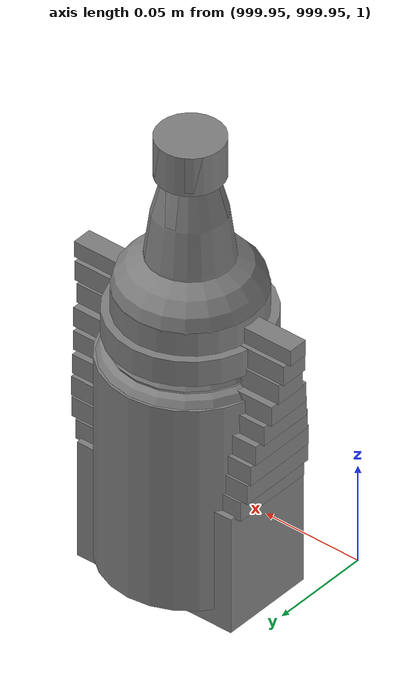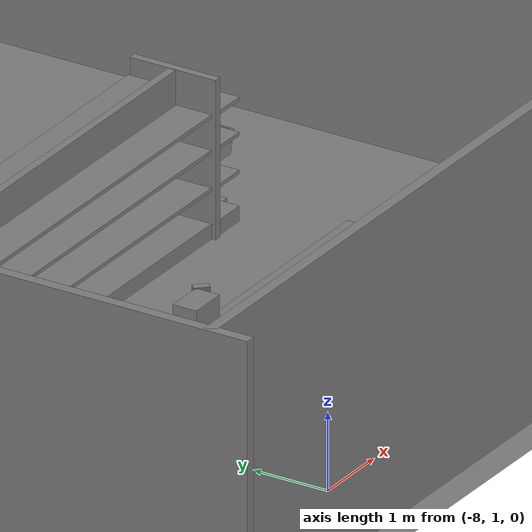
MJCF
<mujoco>
    <option gravity="0.000000000 0.000000000 -9.810000420" timestep="0.0166666" integrator="implicitfast" density="1.225" viscosity="1.8000001e-05" noslip_iterations="10" iterations="100" sdf_iterations="50">
        <flag multiccd="disable"/>
    </option>
    <size memory="1000M"/>
    <compiler coordinate="local"/>
    <worldbody>
        <light cutoff="30" pos="0 1 1" dir="0 -1 -2"/>
        <light cutoff="30" pos="0 -1 1" dir="0 1 -2"/>
        <body pos="-7.168000221 2.823999882 1.227496982" euler="-0.283413976 0.056829724 -0.133293271" name="openloong_gripper_2f85_fix_base_usda_Pos">
            <geom contype="1" conaffinity="1" density="1000" type="box" material="" rgba="0.500000000 0.500000000 0.500000000 1.000000000" solimp="0.899999976 0.949999988 0.001000000" friction="1.000000000 0.005000000 0.000100000" solref="0.020000000 1.000000000" margin="0" condim="3" group="0" pos="-0.002278805 0.074524641 -0.004134059" quat="0.315989345 0.948763072 -0.000000000 0.000000000" size="0.059999999 0.013000000 0.035000000" name="openloong_gripper_2f85_fix_base_usda_geom_88D313EC_253E_4036_A90D_622F6534EF07"/>
            <geom contype="1" conaffinity="1" density="1000" type="box" material="" rgba="0.500000000 0.500000000 0.500000000 1.000000000" solimp="0.899999976 0.949999988 0.001000000" friction="1.000000000 0.005000000 0.000100000" solref="0.020000000 1.000000000" margin="0" condim="3" group="0" pos="-0.002278805 0.078031301 0.008128285" quat="0.990447521 -0.137893379 -0.000000000 -0.000000000" size="0.059999999 0.010000000 0.035000000" name="openloong_gripper_2f85_fix_base_usda_geom_2404BF8C_2D48_4AEC_8A05_976DB92A705E"/>
            <geom contype="1" conaffinity="1" density="1000" type="box" material="" rgba="0.500000000 0.500000000 0.500000000 1.000000000" solimp="0.899999976 0.949999988 0.001000000" friction="1.000000000 0.005000000 0.000100000" solref="0.020000000 1.000000000" margin="0" condim="3" group="0" pos="-0.002278805 0.080785275 -0.002596974" quat="0.287325472 -0.957833409 0.000000000 -0.000000000" size="0.059999999 0.013000000 0.035000000" name="openloong_gripper_2f85_fix_base_usda_geom_BB7B24CC_7B92_4AA4_92AB_3225BBF221E1"/>
            <geom contype="1" conaffinity="1" density="1000" type="box" material="" rgba="0.500000000 0.500000000 0.500000000 1.000000000" solimp="0.899999976 0.949999988 0.001000000" friction="1.000000000 0.005000000 0.000100000" solref="0.020000000 1.000000000" margin="0" condim="3" group="0" pos="-0.002278805 -0.098804474 -0.020146966" quat="0.988851666 0.148906454 0.000000000 -0.000000000" size="0.059999999 0.022000000 0.020000000" name="openloong_gripper_2f85_fix_base_usda_geom_7B5037BB_3CDD_478A_AF65_D46EDAD9C225"/>
            <geom contype="1" conaffinity="1" density="1000" type="box" material="" rgba="0.500000000 0.500000000 0.500000000 1.000000000" solimp="0.899999976 0.949999988 0.001000000" friction="1.000000000 0.005000000 0.000100000" solref="0.020000000 1.000000000" margin="0" condim="3" group="0" pos="-0.002279282 0.019920111 0.012102962" quat="0.995421767 0.095583342 -0.000000000 -0.000000000" size="0.059999999 0.025000000 0.026000001" name="openloong_gripper_2f85_fix_base_usda_geom_6E44AAA5_DB59_4423_9B6B_F30ACDEA4DDB"/>
            <geom contype="1" conaffinity="1" density="1000" type="box" material="" rgba="0.500000000 0.500000000 0.500000000 1.000000000" solimp="0.899999976 0.949999988 0.001000000" friction="1.000000000 0.005000000 0.000100000" solref="0.020000000 1.000000000" margin="0" condim="3" group="0" pos="-0.002279282 0.005734444 -0.014276862" quat="0.999571741 -0.029275302 -0.000000000 -0.000000000" size="0.059999999 0.050000001 0.010000000" name="openloong_gripper_2f85_fix_base_usda_geom_C0ABF991_43B0_47BD_9118_060D1FE036DD"/>
            <geom contype="1" conaffinity="1" density="1000" type="box" material="" rgba="0.500000000 0.500000000 0.500000000 1.000000000" solimp="0.899999976 0.949999988 0.001000000" friction="1.000000000 0.005000000 0.000100000" solref="0.020000000 1.000000000" margin="0" condim="3" group="0" pos="-0.002278805 0.079460382 0.007771969" quat="0.922590554 -0.385781586 0.000000000 -0.000000000" size="0.059999999 0.010000000 0.035000000" name="openloong_gripper_2f85_fix_base_usda_geom_32738F49_56CD_41D6_93BB_48A7492C5FE9"/>
            <geom contype="1" conaffinity="1" density="1000" type="box" material="" rgba="0.500000000 0.500000000 0.500000000 1.000000000" solimp="0.899999976 0.949999988 0.001000000" friction="1.000000000 0.005000000 0.000100000" solref="0.020000000 1.000000000" margin="0" condim="3" group="0" pos="-0.002279282 0.081384182 -0.001320124" quat="0.590483785 -0.807049930 0.000000000 -0.000000000" size="0.059999999 0.013000000 0.035000000" name="openloong_gripper_2f85_fix_base_usda_geom_859F5575_4358_4789_9A12_17818896FB9D"/>
            <geom contype="1" conaffinity="1" density="1000" type="box" material="" rgba="0.500000000 0.500000000 0.500000000 1.000000000" solimp="0.899999976 0.949999988 0.001000000" friction="1.000000000 0.005000000 0.000100000" solref="0.020000000 1.000000000" margin="0" condim="3" group="0" pos="-0.002278805 -0.059297800 -0.007972836" quat="0.988851666 0.148906454 0.000000000 -0.000000000" size="0.059999999 0.020000000 0.022000000" name="openloong_gripper_2f85_fix_base_usda_geom_76067E0D_F140_4364_8412_188974EB5B90"/>
            <geom contype="1" conaffinity="1" density="1000" type="box" material="" rgba="0.500000000 0.500000000 0.500000000 1.000000000" solimp="0.899999976 0.949999988 0.001000000" friction="1.000000000 0.005000000 0.000100000" solref="0.020000000 1.000000000" margin="0" condim="3" group="0" pos="-0.002278805 0.076618671 -0.004656792" quat="0.004634961 0.999989629 -0.000000000 0.000000000" size="0.059999999 0.013000000 0.035000000" name="openloong_gripper_2f85_fix_base_usda_geom_B5FAA738_350A_4F65_BFF2_1E0ABC9923CD"/>
            <geom contype="1" conaffinity="1" density="1000" type="box" material="" rgba="0.500000000 0.500000000 0.500000000 1.000000000" solimp="0.899999976 0.949999988 0.001000000" friction="1.000000000 0.005000000 0.000100000" solref="0.020000000 1.000000000" margin="0" condim="3" group="0" pos="-0.002279282 -0.021952629 0.002960086" quat="0.991270423 0.131847665 -0.000000000 0.000000000" size="0.059999999 0.020000000 0.024000000" name="openloong_gripper_2f85_fix_base_usda_geom_4454C545_209F_4C94_AC79_B8E57059F0C6"/>
            <geom contype="1" conaffinity="1" density="1000" type="box" material="" rgba="0.500000000 0.500000000 0.500000000 1.000000000" solimp="0.899999976 0.949999988 0.001000000" friction="1.000000000 0.005000000 0.000100000" solref="0.020000000 1.000000000" margin="0" condim="3" group="0" pos="-0.002278805 0.081418991 0.002587914" quat="0.803492308 -0.595315695 0.000000000 -0.000000000" size="0.059999999 0.013000000 0.035000000" name="openloong_gripper_2f85_fix_base_usda_geom_10F0CC49_78B0_442E_8B21_C2EF0D715045"/>
            <geom contype="1" conaffinity="1" density="1000" type="box" material="" rgba="0.500000000 0.500000000 0.500000000 1.000000000" solimp="0.899999976 0.949999988 0.001000000" friction="1.000000000 0.005000000 0.000100000" solref="0.020000000 1.000000000" margin="0" condim="3" group="0" pos="-0.002278805 0.061115503 0.008545756" quat="0.999326169 0.036714450 0.000000000 -0.000000000" size="0.059999999 0.020000000 0.035000000" name="openloong_gripper_2f85_fix_base_usda_geom_757D1758_CAD1_4652_89B6_2D60EDE52A7C"/>
            <freejoint name="openloong_gripper_2f85_fix_base_usda_pos_scan"/>
        </body>
        <body pos="-2.436573029 6.404376507 0.137849092" euler="0.000000000 0.000000000 0.000000000" name="openloong_gripper_2f85_fix_base_usda_shoppingtrolley_01">
            <geom contype="1" conaffinity="1" density="1000" type="box" material="" rgba="0.500000000 0.500000000 0.500000000 1.000000000" solimp="0.899999976 0.949999988 0.001000000" friction="1.000000000 0.005000000 0.000100000" solref="0.020000000 1.000000000" margin="0" condim="3" group="0" pos="-0.169898406 -0.178061336 0.864131629" quat="0.916343808 -0.400392294 -0.000000045 0.000000030" size="0.017999999 0.022499999 0.089999996" name="openloong_gripper_2f85_fix_base_usda_geom_55B5B2AF_787E_4CD9_B75F_4EF1693957D1"/>
            <geom contype="1" conaffinity="1" density="1000" type="box" material="" rgba="0.500000000 0.500000000 0.500000000 1.000000000" solimp="0.899999976 0.949999988 0.001000000" friction="1.000000000 0.005000000 0.000100000" solref="0.020000000 1.000000000" margin="0" condim="3" group="0" pos="-0.107458733 0.238907143 0.911498845" quat="0.634576976 0.622505128 -0.330067992 -0.317575932" size="0.017999999 0.022499999 0.035999998" name="openloong_gripper_2f85_fix_base_usda_geom_BEC49F30_E68D_416C_8697_48CC510EF702"/>
            <geom contype="1" conaffinity="1" density="1000" type="box" material="" rgba="0.500000000 0.500000000 0.500000000 1.000000000" solimp="0.899999976 0.949999988 0.001000000" friction="1.000000000 0.005000000 0.000100000" solref="0.020000000 1.000000000" margin="0" condim="3" group="0" pos="-0.005004787 0.248085022 0.912686050" quat="1.000000000 0.000000000 0.000000000 0.000000000" size="0.107999995 0.022499999 0.022499999" name="openloong_gripper_2f85_fix_base_usda_geom_3F19D947_351D_4C33_8DDD_1765472AB6A6"/>
            <geom contype="1" conaffinity="1" density="1000" type="box" material="" rgba="0.500000000 0.500000000 0.500000000 1.000000000" solimp="0.899999976 0.949999988 0.001000000" friction="1.000000000 0.005000000 0.000100000" solref="0.020000000 1.000000000" margin="0" condim="3" group="0" pos="0.131482959 -0.182533979 0.598989725" quat="0.996607125 0.055331629 0.059003670 0.015205893" size="0.013499999 0.287999988 0.053999998" name="openloong_gripper_2f85_fix_base_usda_geom_099A7770_BF20_4C24_AD72_DE47CE977695"/>
            <geom contype="1" conaffinity="1" density="1000" type="box" material="" rgba="0.500000000 0.500000000 0.500000000 1.000000000" solimp="0.899999976 0.949999988 0.001000000" friction="1.000000000 0.005000000 0.000100000" solref="0.020000000 1.000000000" margin="0" condim="3" group="0" pos="-0.000005364 0.100332208 0.734785020" quat="0.999668717 0.025737956 -0.000000010 0.000000000" size="0.135000005 0.019800000 0.152999997" name="openloong_gripper_2f85_fix_base_usda_geom_52621823_014E_4801_9951_834E3CB7AF76"/>
            <geom contype="1" conaffinity="1" density="1000" type="box" material="" rgba="0.500000000 0.500000000 0.500000000 1.000000000" solimp="0.899999976 0.949999988 0.001000000" friction="1.000000000 0.005000000 0.000100000" solref="0.020000000 1.000000000" margin="0" condim="3" group="0" pos="-0.126757339 -0.182533979 0.598989725" quat="0.996607184 0.055331606 -0.059003651 -0.015205891" size="0.013499999 0.287999988 0.053999998" name="openloong_gripper_2f85_fix_base_usda_geom_DE41452D_BD16_4D27_A473_6EF856DB1F3A"/>
            <geom contype="1" conaffinity="1" density="1000" type="box" material="" rgba="0.500000000 0.500000000 0.500000000 1.000000000" solimp="0.899999976 0.949999988 0.001000000" friction="1.000000000 0.005000000 0.000100000" solref="0.020000000 1.000000000" margin="0" condim="3" group="0" pos="-0.134013891 0.200098798 0.912192523" quat="0.694057047 0.679413557 -0.172947660 -0.163618833" size="0.017999999 0.022499999 0.035999998" name="openloong_gripper_2f85_fix_base_usda_geom_5BDEA7B2_3187_43F0_96E3_C80B916CE753"/>
            <geom contype="1" conaffinity="1" density="1000" type="box" material="" rgba="0.500000000 0.500000000 0.500000000 1.000000000" solimp="0.899999976 0.949999988 0.001000000" friction="1.000000000 0.005000000 0.000100000" solref="0.020000000 1.000000000" margin="0" condim="3" group="0" pos="0.141839072 -0.191051379 0.702451229" quat="0.997147262 0.056065105 0.045779929 0.021407485" size="0.013499999 0.287999988 0.053999998" name="openloong_gripper_2f85_fix_base_usda_geom_B9BC0595_006D_40D6_BA85_6AC420E712BB"/>
            <geom contype="1" conaffinity="1" density="1000" type="box" material="" rgba="0.500000000 0.500000000 0.500000000 1.000000000" solimp="0.899999976 0.949999988 0.001000000" friction="1.000000000 0.005000000 0.000100000" solref="0.020000000 1.000000000" margin="0" condim="3" group="0" pos="-0.135714188 -0.191051379 0.694841146" quat="0.997147322 0.056064609 -0.045779683 -0.021407485" size="0.013499999 0.287999988 0.053999998" name="openloong_gripper_2f85_fix_base_usda_geom_DDC95BEA_40BF_4B52_9AEB_4723F0911EB5"/>
            <geom contype="1" conaffinity="1" density="1000" type="box" material="" rgba="0.500000000 0.500000000 0.500000000 1.000000000" solimp="0.899999976 0.949999988 0.001000000" friction="1.000000000 0.005000000 0.000100000" solref="0.020000000 1.000000000" margin="0" condim="3" group="0" pos="-0.000004721 -0.174527690 0.560063601" quat="0.996704638 0.081116498 -0.000000004 0.000000000" size="0.126000002 0.287999988 0.009000000" name="openloong_gripper_2f85_fix_base_usda_geom_257DFDE3_479A_4F79_B4A1_9B3ABC124119"/>
            <geom contype="1" conaffinity="1" density="1000" type="box" material="" rgba="0.500000000 0.500000000 0.500000000 1.000000000" solimp="0.899999976 0.949999988 0.001000000" friction="1.000000000 0.005000000 0.000100000" solref="0.020000000 1.000000000" margin="0" condim="3" group="0" pos="0.134013891 0.200098798 0.912192523" quat="0.692574680 -0.680924535 -0.166899428 0.169783980" size="0.017999999 0.022499999 0.035999998" name="openloong_gripper_2f85_fix_base_usda_geom_6BC4178C_143D_487A_B05A_EC0C63CEB057"/>
            <geom contype="1" conaffinity="1" density="1000" type="box" material="" rgba="0.500000000 0.500000000 0.500000000 1.000000000" solimp="0.899999976 0.949999988 0.001000000" friction="1.000000000 0.005000000 0.000100000" solref="0.020000000 1.000000000" margin="0" condim="3" group="0" pos="-0.012634277 -0.174527690 -0.088243507" quat="1.000000000 0.000000000 -0.000000004 0.000000000" size="0.135000005 0.287999988 0.044999998" name="openloong_gripper_2f85_fix_base_usda_geom_30C9C649_22EE_4D65_A2B3_F142B9B6F99D"/>
            <geom contype="1" conaffinity="1" density="1000" type="box" material="" rgba="0.500000000 0.500000000 0.500000000 1.000000000" solimp="0.899999976 0.949999988 0.001000000" friction="1.000000000 0.005000000 0.000100000" solref="0.020000000 1.000000000" margin="0" condim="3" group="0" pos="-0.142927840 -0.199506134 0.784674108" quat="0.998421252 0.016904408 -0.027109101 -0.046199299" size="0.013499999 0.305999994 0.063000001" name="openloong_gripper_2f85_fix_base_usda_geom_564C3EF0_937C_4103_9578_1565B3DEFBD4"/>
            <geom contype="1" conaffinity="1" density="1000" type="box" material="" rgba="0.500000000 0.500000000 0.500000000 1.000000000" solimp="0.899999976 0.949999988 0.001000000" friction="1.000000000 0.005000000 0.000100000" solref="0.020000000 1.000000000" margin="0" condim="3" group="0" pos="-0.169898406 -0.043119621 0.915120542" quat="0.687021017 0.726584017 -0.005590606 -0.006832919" size="0.017999999 0.022499999 0.089999996" name="openloong_gripper_2f85_fix_base_usda_geom_757932F7_E478_400A_A648_A32826E8EEF2"/>
            <geom contype="1" conaffinity="1" density="1000" type="box" material="" rgba="0.500000000 0.500000000 0.500000000 1.000000000" solimp="0.899999976 0.949999988 0.001000000" friction="1.000000000 0.005000000 0.000100000" solref="0.020000000 1.000000000" margin="0" condim="3" group="0" pos="-0.000006008 -0.484932661 0.670727849" quat="0.997585475 0.069449045 -0.000000004 -0.000000089" size="0.179999992 0.013499999 0.170999989" name="openloong_gripper_2f85_fix_base_usda_geom_7FBAAB38_2C6F_4CFA_9DED_CC4974DF9929"/>
            <geom contype="1" conaffinity="1" density="1000" type="box" material="" rgba="0.500000000 0.500000000 0.500000000 1.000000000" solimp="0.899999976 0.949999988 0.001000000" friction="1.000000000 0.005000000 0.000100000" solref="0.020000000 1.000000000" margin="0" condim="3" group="0" pos="0.160832971 0.103427693 0.910528183" quat="0.711112797 -0.700149298 -0.042821646 0.047705106" size="0.017999999 0.022499999 0.071999997" name="openloong_gripper_2f85_fix_base_usda_geom_EC627140_7CEA_45B4_A205_CCC8F0948D84"/>
            <geom contype="1" conaffinity="1" density="1000" type="box" material="" rgba="0.500000000 0.500000000 0.500000000 1.000000000" solimp="0.899999976 0.949999988 0.001000000" friction="1.000000000 0.005000000 0.000100000" solref="0.020000000 1.000000000" margin="0" condim="3" group="0" pos="-0.160832763 0.103427693 0.910528183" quat="0.711469591 0.699786782 -0.048386075 -0.042050660" size="0.017999999 0.022499999 0.071999997" name="openloong_gripper_2f85_fix_base_usda_geom_F083F3C7_CC3D_4698_9B17_2EB36186223F"/>
            <geom contype="1" conaffinity="1" density="1000" type="box" material="" rgba="0.500000000 0.500000000 0.500000000 1.000000000" solimp="0.899999976 0.949999988 0.001000000" friction="1.000000000 0.005000000 0.000100000" solref="0.020000000 1.000000000" margin="0" condim="3" group="0" pos="0.169898629 -0.178061336 0.864131629" quat="0.916343808 -0.400392294 -0.000000045 0.000000030" size="0.017999999 0.022499999 0.089999996" name="openloong_gripper_2f85_fix_base_usda_geom_13016957_D8C4_49D7_B519_F8689DBF7538"/>
            <geom contype="1" conaffinity="1" density="1000" type="box" material="" rgba="0.500000000 0.500000000 0.500000000 1.000000000" solimp="0.899999976 0.949999988 0.001000000" friction="1.000000000 0.005000000 0.000100000" solref="0.020000000 1.000000000" margin="0" condim="3" group="0" pos="0.103667587 0.233050480 0.912927270" quat="0.634205043 -0.622199059 -0.324503720 0.324576139" size="0.017999999 0.022499999 0.035999998" name="openloong_gripper_2f85_fix_base_usda_geom_9DEFA60B_CE6C_45D2_9B33_3639DC34504C"/>
            <geom contype="1" conaffinity="1" density="1000" type="box" material="" rgba="0.500000000 0.500000000 0.500000000 1.000000000" solimp="0.899999976 0.949999988 0.001000000" friction="1.000000000 0.005000000 0.000100000" solref="0.020000000 1.000000000" margin="0" condim="3" group="0" pos="0.169898629 -0.043119621 0.915120542" quat="0.687029123 -0.726576388 -0.006509603 0.005963952" size="0.017999999 0.022499999 0.089999996" name="openloong_gripper_2f85_fix_base_usda_geom_71E5CE4F_544C_4643_BA41_63518B19313A"/>
            <geom contype="1" conaffinity="1" density="1000" type="box" material="" rgba="0.500000000 0.500000000 0.500000000 1.000000000" solimp="0.899999976 0.949999988 0.001000000" friction="1.000000000 0.005000000 0.000100000" solref="0.020000000 1.000000000" margin="0" condim="3" group="0" pos="0.148195267 -0.199506566 0.782808602" quat="0.998808920 0.017156634 0.026950166 0.036880098" size="0.013499999 0.305999994 0.063000001" name="openloong_gripper_2f85_fix_base_usda_geom_C27F69A6_8F0A_44E1_BA80_7A272FF7C1A4"/>
            <freejoint name="openloong_gripper_2f85_fix_base_usda_shoppingtrolley_01_joint"/>
            <site size="0.005000000 0.005000000 0.005000000" rgba="0.500000000 0.500000000 0.500000000 1.000000000" pos="0.000000000 0.000000000 0.000000000" quat="1.000000000 0.000000000 0.000000000 0.000000000" group="0" type="sphere" name="openloong_gripper_2f85_fix_base_usda_shoppingtrolley_01"/>
        </body>
        <body pos="-6.332345009 2.779978037 1.034067392" euler="0.000000000 0.000000000 0.000000000" name="openloong_gripper_2f85_fix_base_usda_basket">
            <geom contype="1" conaffinity="1" density="100000" type="box" material="" rgba="0.500000000 0.500000000 0.500000000 1.000000000" solimp="0.899999976 0.949999988 0.001000000" friction="1.000000000 0.899999976 0.000100000" solref="0.020000000 1.000000000" margin="0" condim="3" group="0" pos="-0.172339439 0.000000000 0.168361664" quat="0.706172407 -0.036353018 -0.036353093 0.706170976" size="0.200000003 0.006000000 0.108000003" name="openloong_gripper_2f85_fix_base_usda_geom_2B2C7BF4_1202_42BF_A1BF_295DFDED8975"/>
            <geom contype="1" conaffinity="1" density="100000" type="box" material="" rgba="0.500000000 0.500000000 0.500000000 1.000000000" solimp="0.899999976 0.949999988 0.001000000" friction="1.000000000 0.899999976 0.000100000" solref="0.020000000 1.000000000" margin="0" condim="3" group="0" pos="-0.039724827 -0.188568115 0.167089701" quat="0.997537494 0.070135131 0.000000000 0.000000000" size="0.150000006 0.006000000 0.108000003" name="openloong_gripper_2f85_fix_base_usda_geom_44323F40_A751_48D3_AF93_0BD0BBBBD35D"/>
            <geom contype="1" conaffinity="1" density="100000" type="box" material="" rgba="0.500000000 0.500000000 0.500000000 1.000000000" solimp="0.899999976 0.949999988 0.001000000" friction="1.000000000 0.899999976 0.000100000" solref="0.020000000 1.000000000" margin="0" condim="3" group="0" pos="-0.039724827 0.188377380 0.167089701" quat="0.997489929 -0.070808925 0.000000000 0.000000000" size="0.150000006 0.006000000 0.108000003" name="openloong_gripper_2f85_fix_base_usda_geom_EFEA3821_7CB6_4BC4_A408_6DE8489321B9"/>
            <geom contype="1" conaffinity="1" density="100000" type="box" material="" rgba="0.500000000 0.500000000 0.500000000 1.000000000" solimp="0.899999976 0.949999988 0.001000000" friction="1.000000000 0.899999976 0.000100000" solref="0.020000000 1.000000000" margin="0" condim="3" group="0" pos="-0.039724827 0.000000000 0.068126202" quat="1.000000000 0.000000000 0.000000000 0.000000000" size="0.129999995 0.174999997 0.006000000" name="openloong_gripper_2f85_fix_base_usda_geom_27E74937_4976_43BE_A9D1_80FC15C18B6B"/>
            <geom contype="1" conaffinity="1" density="100000" type="box" material="" rgba="0.500000000 0.500000000 0.500000000 1.000000000" solimp="0.899999976 0.949999988 0.001000000" friction="1.000000000 0.899999976 0.000100000" solref="0.020000000 1.000000000" margin="0" condim="3" group="0" pos="0.094372749 0.000000000 0.168361664" quat="0.706172049 0.036353335 0.036353379 0.706171215" size="0.200000003 0.006000000 0.108000003" name="openloong_gripper_2f85_fix_base_usda_geom_E279B7FD_8EBA_4FD1_8CA4_03FD5C73C311"/>
            <freejoint name="openloong_gripper_2f85_fix_base_usda_basket_joint"/>
            <site size="0.005000000 0.005000000 0.005000000" rgba="0.500000000 0.500000000 0.500000000 1.000000000" pos="0.000000000 0.000000000 0.000000000" quat="1.000000000 0.000000000 0.000000000 0.000000000" group="0" type="sphere" name="openloong_gripper_2f85_fix_base_usda_basketsite"/>
        </body>
        <body pos="-3.510578632 3.403555870 -0.000000100" euler="0.000000000 0.000000000 40.200675964" name="openloong_gripper_2f85_fix_base_usda_PZ">
            <geom contype="1" conaffinity="1" density="1000" type="box" material="" rgba="0.500000000 0.500000000 0.500000000 1.000000000" solimp="0.899999976 0.949999988 0.001000000" friction="1.000000000 0.005000000 0.000100000" solref="0.020000000 1.000000000" margin="0" condim="3" group="0" pos="-0.047453165 0.056484699 0.373715430" quat="0.934750080 0.077914521 0.028795123 0.345459938" size="0.180000007 0.010000000 0.379999995" name="openloong_gripper_2f85_fix_base_usda_geom_1A5736F7_E883_4998_A42C_EB7D552C54CC"/>
            <geom contype="1" conaffinity="1" density="1000" type="box" material="" rgba="0.500000000 0.500000000 0.500000000 1.000000000" solimp="0.899999976 0.949999988 0.001000000" friction="1.000000000 0.005000000 0.000100000" solref="0.020000000 1.000000000" margin="0" condim="3" group="0" pos="0.047452450 -0.054376602 0.374072611" quat="0.934387863 -0.082143910 -0.030358355 0.345326364" size="0.180000007 0.010000000 0.379999995" name="openloong_gripper_2f85_fix_base_usda_geom_B1AA3738_C278_4F11_A7CE_46077BAB277B"/>
            <freejoint name="openloong_gripper_2f85_fix_base_usda_PZ"/>
        </body>
        <body pos="0.000000000 0.000000000 0.000000000" euler="0.000000000 0.000000000 0.000000000" name="Interactive Objects_Interactive Objects"/>
        <body pos="0.000000000 0.000000000 0.000000000" euler="0.000000000 0.000000000 0.000000000" name=" Static Objects_ Static Objects">
            <geom contype="1" conaffinity="1" density="1000" type="box" material="" rgba="0.500000000 0.500000000 0.500000000 1.000000000" solimp="0.899999976 0.949999988 0.001000000" friction="1.000000000 0.005000000 0.000100000" solref="0.020000000 1.000000000" margin="0" condim="3" group="0" pos="-3.101639986 6.150595188 1.018643856" quat="1.000000000 0.000000000 0.000000000 0.000000000" size="0.050000001 0.579999983 1.019999981" name=" Static Objects_geom_20B47E63_2D0B_4738_A410_E4519FC57B8B"/>
            <geom contype="1" conaffinity="1" density="1000" type="box" material="" rgba="0.500000000 0.500000000 0.500000000 1.000000000" solimp="0.899999976 0.949999988 0.001000000" friction="1.000000000 0.005000000 0.000100000" solref="0.020000000 1.000000000" margin="0" condim="3" group="0" pos="-2.825197220 6.153595448 1.115278244" quat="0.707107067 0.000000000 0.000000000 0.707106471" size="0.550000012 0.239999995 0.025000000" name=" Static Objects_geom_EA1344BE_5BD8_49F1_8B86_1043680568EB"/>
            <geom contype="1" conaffinity="1" density="1000" type="box" material="" rgba="0.500000000 0.500000000 0.500000000 1.000000000" solimp="0.899999976 0.949999988 0.001000000" friction="1.000000000 0.005000000 0.000100000" solref="0.020000000 1.000000000" margin="0" condim="3" group="0" pos="-2.825197220 6.153595448 0.097434282" quat="0.707107067 0.000000000 0.000000000 0.707106471" size="0.550000012 0.239999995 0.098999999" name=" Static Objects_geom_56A59E63_FB2B_42EE_B72B_3F13AA357679"/>
            <geom contype="1" conaffinity="1" density="1000" type="box" material="" rgba="0.500000000 0.500000000 0.500000000 1.000000000" solimp="0.899999976 0.949999988 0.001000000" friction="1.000000000 0.005000000 0.000100000" solref="0.020000000 1.000000000" margin="0" condim="3" group="0" pos="-6.293097973 6.153595448 1.114443064" quat="0.707107067 0.000000000 0.000000000 0.707106471" size="0.529999971 3.134999990 0.025000000" name=" Static Objects_geom_DC6882AE_BEB8_4F9F_9028_5A6246D6AAC1"/>
            <geom contype="1" conaffinity="1" density="1000" type="box" material="" rgba="0.500000000 0.500000000 0.500000000 1.000000000" solimp="0.899999976 0.949999988 0.001000000" friction="1.000000000 0.005000000 0.000100000" solref="0.020000000 1.000000000" margin="0" condim="3" group="0" pos="-6.286010742 6.153595448 0.096129179" quat="0.707107067 0.000000000 0.000000000 0.707106471" size="0.529999971 3.134999990 0.098999999" name=" Static Objects_geom_9FD36F0C_CBFE_4EA9_830E_CB5279990AFE"/>
            <geom contype="1" conaffinity="1" density="1000" type="box" material="" rgba="0.500000000 0.500000000 0.500000000 1.000000000" solimp="0.899999976 0.949999988 0.001000000" friction="1.000000000 0.005000000 0.000100000" solref="0.020000000 1.000000000" margin="0" condim="3" group="0" pos="-2.825197220 6.153595448 1.563861728" quat="0.707107067 0.000000000 0.000000000 0.707106471" size="0.550000012 0.239999995 0.025000000" name=" Static Objects_geom_CB216615_2F7E_4911_92EB_69513D4F6E7D"/>
            <geom contype="1" conaffinity="1" density="1000" type="box" material="" rgba="0.500000000 0.500000000 0.500000000 1.000000000" solimp="0.899999976 0.949999988 0.001000000" friction="1.000000000 0.005000000 0.000100000" solref="0.020000000 1.000000000" margin="0" condim="3" group="0" pos="-6.311686516 6.153595448 1.018643856" quat="0.707107067 0.000000000 0.000000000 0.707106471" size="0.050000001 3.150000095 1.019999981" name=" Static Objects_geom_369FF323_D613_4949_BACF_3BB3553F3625"/>
            <geom contype="1" conaffinity="1" density="1000" type="box" material="" rgba="0.500000000 0.500000000 0.500000000 1.000000000" solimp="0.899999976 0.949999988 0.001000000" friction="1.000000000 0.005000000 0.000100000" solref="0.020000000 1.000000000" margin="0" condim="3" group="0" pos="-2.825197220 6.153595448 0.629031777" quat="0.707107067 0.000000000 0.000000000 0.707106471" size="0.550000012 0.239999995 0.025000000" name=" Static Objects_geom_3F0206A2_C483_45D1_B903_8E1EF1A14923"/>
            <geom contype="1" conaffinity="1" density="1000" type="box" material="" rgba="0.500000000 0.500000000 0.500000000 1.000000000" solimp="0.899999976 0.949999988 0.001000000" friction="1.000000000 0.005000000 0.000100000" solref="0.020000000 1.000000000" margin="0" condim="3" group="0" pos="-6.286010742 6.153595448 1.563861728" quat="0.707107067 0.000000000 0.000000000 0.707106471" size="0.529999971 3.134999990 0.025000000" name=" Static Objects_geom_2D098570_91AF_4BFB_A714_4292A2557985"/>
            <geom contype="1" conaffinity="1" density="1000" type="box" material="" rgba="0.500000000 0.500000000 0.500000000 1.000000000" solimp="0.899999976 0.949999988 0.001000000" friction="1.000000000 0.005000000 0.000100000" solref="0.020000000 1.000000000" margin="0" condim="3" group="0" pos="-6.286010742 6.153595448 0.629031777" quat="0.707107067 0.000000000 0.000000000 0.707106471" size="0.529999971 3.134999990 0.025000000" name=" Static Objects_geom_4E7DA4E7_39E2_4CD1_9B4E_A36E7341584D"/>
            <geom contype="1" conaffinity="1" density="1000" type="box" material="" rgba="0.500000000 0.500000000 0.500000000 1.000000000" solimp="0.899999976 0.949999988 0.001000000" friction="1.000000000 0.005000000 0.000100000" solref="0.020000000 1.000000000" margin="0" condim="3" group="0" pos="-7.719123363 2.867671013 1.173410416" quat="1.000000000 0.000000000 0.000000000 0.000000000" size="0.250000000 0.250000000 0.079999998" name=" Static Objects_geom_5FF56E8E_CB10_46B3_85DB_7B072954BA94"/>
            <geom contype="1" conaffinity="1" density="1000" type="box" material="" rgba="0.500000000 0.500000000 0.500000000 1.000000000" solimp="0.899999976 0.949999988 0.001000000" friction="1.000000000 0.005000000 0.000100000" solref="0.020000000 1.000000000" margin="0" condim="3" group="0" pos="-7.408766270 3.088089943 1.776644945" quat="0.928051054 0.000000000 0.000000000 0.372453064" size="0.050000001 0.100000001 0.050000001" name=" Static Objects_geom_960BCFBA_DCFF_4DB5_B321_21CB77227078"/>
            <geom contype="1" conaffinity="1" density="1000" type="box" material="" rgba="0.500000000 0.500000000 0.500000000 1.000000000" solimp="0.899999976 0.949999988 0.001000000" friction="1.000000000 0.005000000 0.000100000" solref="0.020000000 1.000000000" margin="0" condim="3" group="0" pos="-7.719123363 2.958004713 1.530241251" quat="1.000000000 0.000000000 0.000000000 0.000000000" size="0.250000000 0.159999996 0.280000001" name=" Static Objects_geom_284B5F1F_CDC7_4C58_B754_2F494A755F82"/>
            <geom contype="1" conaffinity="1" density="1000" type="cylinder" material="" rgba="0.500000000 0.500000000 0.500000000 1.000000000" solimp="0.899999976 0.949999988 0.001000000" friction="1.000000000 0.005000000 0.000100000" solref="0.020000000 1.000000000" margin="0" condim="3" group="0" pos="-7.427312374 3.069516420 1.502544641" quat="0.928051054 0.000000000 0.000000000 0.372453064" size="0.015000000 0.230000004 0.100000001" name=" Static Objects_geom_8CA91F11_E944_4F6F_B42F_F46529A6213D"/>
            <geom contype="1" conaffinity="1" density="1000" type="box" material="" rgba="0.500000000 0.500000000 0.500000000 1.000000000" solimp="0.899999976 0.949999988 0.001000000" friction="1.000000000 0.005000000 0.000100000" solref="0.020000000 1.000000000" margin="0" condim="3" group="0" pos="-7.437745571 3.067511320 1.289965630" quat="1.000000000 0.000000000 0.000000000 0.000000000" size="0.029999999 0.020000000 0.020000000" name=" Static Objects_geom_3259DEF9_5A0B_46F9_8804_FDBC14F318A7"/>
            <geom contype="1" conaffinity="1" density="1000" type="box" material="" rgba="0.500000000 0.500000000 0.500000000 1.000000000" solimp="0.899999976 0.949999988 0.001000000" friction="1.000000000 0.005000000 0.000100000" solref="0.020000000 1.000000000" margin="0" condim="3" group="0" pos="-9.058088303 6.434794426 1.209077358" quat="1.000000000 0.000000000 0.000000000 0.000000000" size="0.250000000 0.100000001 0.070000000" name=" Static Objects_geom_D1958037_39D1_4069_A476_A670042C53DC"/>
            <geom contype="1" conaffinity="1" density="1000" type="box" material="" rgba="0.500000000 0.500000000 0.500000000 1.000000000" solimp="0.899999976 0.949999988 0.001000000" friction="1.000000000 0.005000000 0.000100000" solref="0.020000000 1.000000000" margin="0" condim="3" group="0" pos="-7.886891365 6.459744930 0.352518857" quat="1.000000000 0.000000000 0.000000000 0.000000000" size="1.500000000 0.200000003 0.150000006" name=" Static Objects_geom_1330247C_0D2D_4FFE_AB19_5AFE761EB0B6"/>
            <geom contype="1" conaffinity="1" density="1000" type="box" material="" rgba="0.500000000 0.500000000 0.500000000 1.000000000" solimp="0.899999976 0.949999988 0.001000000" friction="1.000000000 0.005000000 0.000100000" solref="0.020000000 1.000000000" margin="0" condim="3" group="0" pos="-9.237723351 6.464855671 1.209077358" quat="1.000000000 0.000000000 0.000000000 0.000000000" size="0.100000001 0.100000001 0.070000000" name=" Static Objects_geom_A77D92DD_3CB9_440A_A5ED_9D23122872B2"/>
            <geom contype="1" conaffinity="1" density="1000" type="box" material="" rgba="0.500000000 0.500000000 0.500000000 1.000000000" solimp="0.899999976 0.949999988 0.001000000" friction="1.000000000 0.005000000 0.000100000" solref="0.020000000 1.000000000" margin="0" condim="3" group="0" pos="-6.924745083 6.362090111 1.214329123" quat="1.000000000 0.000000000 0.000000000 0.000000000" size="0.200000003 0.100000001 0.075000003" name=" Static Objects_geom_9D944363_3A7B_4673_8E47_58B359DE5E64"/>
            <geom contype="1" conaffinity="1" density="1000" type="box" material="" rgba="0.500000000 0.500000000 0.500000000 1.000000000" solimp="0.899999976 0.949999988 0.001000000" friction="1.000000000 0.005000000 0.000100000" solref="0.020000000 1.000000000" margin="0" condim="3" group="0" pos="-4.407354832 6.459744930 1.292199373" quat="1.000000000 0.000000000 0.000000000 0.000000000" size="1.240000010 0.200000003 0.150000006" name=" Static Objects_geom_40C640D0_0BA6_490A_879A_AC684DDEF0A6"/>
            <geom contype="1" conaffinity="1" density="1000" type="box" material="" rgba="0.500000000 0.500000000 0.500000000 1.000000000" solimp="0.899999976 0.949999988 0.001000000" friction="1.000000000 0.005000000 0.000100000" solref="0.020000000 1.000000000" margin="0" condim="3" group="0" pos="-5.611940861 6.318420410 0.350975692" quat="1.000000000 0.000000000 0.000000000 0.000000000" size="0.699999988 0.100000001 0.150000006" name=" Static Objects_geom_2D20C069_0D7A_470A_95B1_06B72750FB2B"/>
            <geom contype="1" conaffinity="1" density="1000" type="box" material="" rgba="0.500000000 0.500000000 0.500000000 1.000000000" solimp="0.899999976 0.949999988 0.001000000" friction="1.000000000 0.005000000 0.000100000" solref="0.020000000 1.000000000" margin="0" condim="3" group="0" pos="-6.300771236 6.459744930 1.744376063" quat="1.000000000 0.000000000 0.000000000 0.000000000" size="3.000000000 0.200000003 0.150000006" name=" Static Objects_geom_97851AEB_41D4_4BD6_8671_51DDE6E50237"/>
            <geom contype="1" conaffinity="1" density="1000" type="box" material="" rgba="0.500000000 0.500000000 0.500000000 1.000000000" solimp="0.899999976 0.949999988 0.001000000" friction="1.000000000 0.005000000 0.000100000" solref="0.020000000 1.000000000" margin="0" condim="3" group="0" pos="-6.751636982 6.459744930 0.800981164" quat="1.000000000 0.000000000 0.000000000 0.000000000" size="2.200000048 0.200000003 0.150000006" name=" Static Objects_geom_F0AA214A_27E7_405B_860A_D15D8DC41E3F"/>
            <geom contype="1" conaffinity="1" density="1000" type="box" material="" rgba="0.500000000 0.500000000 0.500000000 1.000000000" solimp="0.899999976 0.949999988 0.001000000" friction="1.000000000 0.005000000 0.000100000" solref="0.020000000 1.000000000" margin="0" condim="3" group="0" pos="-8.844120979 6.464855671 1.209077358" quat="1.000000000 0.000000000 0.000000000 0.000000000" size="0.100000001 0.100000001 0.070000000" name=" Static Objects_geom_9F00C56C_0ABA_4BE2_A5F4_DE7922AAC54A"/>
            <geom contype="1" conaffinity="1" density="1000" type="box" material="" rgba="0.500000000 0.500000000 0.500000000 1.000000000" solimp="0.899999976 0.949999988 0.001000000" friction="1.000000000 0.005000000 0.000100000" solref="0.020000000 1.000000000" margin="0" condim="3" group="0" pos="-6.098561764 6.327973843 1.292199373" quat="1.000000000 0.000000000 0.000000000 0.000000000" size="0.500000000 0.100000001 0.150000006" name=" Static Objects_geom_7D5342FE_0639_435A_A5C8_9206AEDE899F"/>
            <geom contype="1" conaffinity="1" density="1000" type="box" material="" rgba="0.500000000 0.500000000 0.500000000 1.000000000" solimp="0.899999976 0.949999988 0.001000000" friction="1.000000000 0.005000000 0.000100000" solref="0.020000000 1.000000000" margin="0" condim="3" group="0" pos="-6.824534416 6.447464466 1.212718010" quat="1.000000000 0.000000000 0.000000000 0.000000000" size="0.100000001 0.100000001 0.075000003" name=" Static Objects_geom_2BF3EEAD_C8D5_4FBC_B3A7_A0FA0DA12994"/>
            <geom contype="1" conaffinity="1" density="1000" type="box" material="" rgba="0.500000000 0.500000000 0.500000000 1.000000000" solimp="0.899999976 0.949999988 0.001000000" friction="1.000000000 0.005000000 0.000100000" solref="0.020000000 1.000000000" margin="0" condim="3" group="0" pos="-3.907610416 6.318625927 0.800981164" quat="1.000000000 0.000000000 0.000000000 0.000000000" size="0.500000000 0.100000001 0.150000006" name=" Static Objects_geom_F4BFA6D6_CB7A_48EB_9C18_7E7E35C7EA4A"/>
            <geom contype="1" conaffinity="1" density="1000" type="box" material="" rgba="0.500000000 0.500000000 0.500000000 1.000000000" solimp="0.899999976 0.949999988 0.001000000" friction="1.000000000 0.005000000 0.000100000" solref="0.020000000 1.000000000" margin="0" condim="3" group="0" pos="-7.373087406 6.458900928 1.214329123" quat="1.000000000 0.000000000 0.000000000 0.000000000" size="0.250000000 0.200000003 0.075000003" name=" Static Objects_geom_F825F980_FD5A_4050_9419_1510A003D2B9"/>
            <geom contype="1" conaffinity="1" density="1000" type="box" material="" rgba="0.500000000 0.500000000 0.500000000 1.000000000" solimp="0.899999976 0.949999988 0.001000000" friction="1.000000000 0.005000000 0.000100000" solref="0.020000000 1.000000000" margin="0" condim="3" group="0" pos="-4.035642624 6.459744930 0.352518857" quat="1.000000000 0.000000000 0.000000000 0.000000000" size="0.800000012 0.200000003 0.150000006" name=" Static Objects_geom_91D007FC_EF86_4724_9C51_44D62DAA3DF7"/>
            <geom contype="1" conaffinity="1" density="1000" type="box" material="" rgba="0.500000000 0.500000000 0.500000000 1.000000000" solimp="0.899999976 0.949999988 0.001000000" friction="1.000000000 0.005000000 0.000100000" solref="0.020000000 1.000000000" margin="0" condim="3" group="0" pos="-6.460197449 2.937205315 0.548931718" quat="1.000000000 0.000000000 0.000000000 0.000000000" size="2.650000095 0.430000007 0.550000012" name=" Static Objects_geom_FBE50C58_174C_4EAA_8F1F_3AA149339BF9"/>
            <geom contype="1" conaffinity="1" density="1000" type="box" material="" rgba="0.500000000 0.500000000 0.500000000 1.000000000" solimp="0.899999976 0.949999988 0.001000000" friction="1.000000000 0.005000000 0.000100000" solref="0.020000000 1.000000000" margin="0" condim="3" group="0" pos="-4.240264893 1.327049494 0.549888909" quat="1.000000000 0.000000000 0.000000000 0.000000000" size="0.430000007 1.200000048 0.550000012" name=" Static Objects_geom_A2A8530A_FC4E_4BD6_8E29_16C8421F0E1A"/>
            <geom contype="1" conaffinity="1" density="1000" type="box" material="" rgba="0.500000000 0.500000000 0.500000000 1.000000000" solimp="0.899999976 0.949999988 0.001000000" friction="1.000000000 0.005000000 0.000100000" solref="0.020000000 1.000000000" margin="0" condim="3" group="0" pos="-8.830721855 2.096410990 0.549305558" quat="1.000000000 0.000000000 0.000000000 0.000000000" size="0.280000001 0.430000007 0.550000012" name=" Static Objects_geom_64022821_4BD3_41DA_909D_2B0631F75D6D"/>
            <geom contype="1" conaffinity="1" density="1000" type="plane" material="" rgba="0.500000000 0.500000000 0.500000000 1.000000000" solimp="0.899999976 0.949999988 0.001000000" friction="1.000000000 0.005000000 0.000100000" solref="0.020000000 1.000000000" margin="0" condim="3" group="0" pos="-6.000000000 10.399999619 0.000000000" quat="1.000000000 0.000000000 0.000000000 0.000000000" size="6.050000191 10.800000191 0.010000000" name=" Static Objects_geom_1EF2E02B_6B26_41FF_BF4F_5A157319A163"/>
            <geom contype="1" conaffinity="1" density="1000" type="box" material="" rgba="0.500000000 0.500000000 0.500000000 1.000000000" solimp="0.899999976 0.949999988 0.001000000" friction="1.000000000 0.005000000 0.000100000" solref="0.020000000 1.000000000" margin="0" condim="3" group="0" pos="-6.000000000 0.035000000 2.000000000" quat="1.000000000 0.000000000 0.000000000 0.000000000" size="6.079999924 0.070000000 2.000000000" name=" Static Objects_geom_74CF5F05_3F72_4EC1_800A_C55CB6A0A240"/>
            <geom contype="1" conaffinity="1" density="1000" type="box" material="" rgba="0.500000000 0.500000000 0.500000000 1.000000000" solimp="0.899999976 0.949999988 0.001000000" friction="1.000000000 0.005000000 0.000100000" solref="0.020000000 1.000000000" margin="0" condim="3" group="0" pos="-6.000000000 20.159999847 2.000000000" quat="1.000000000 0.000000000 0.000000000 0.000000000" size="6.079999924 0.070000000 2.000000000" name=" Static Objects_geom_DC68C82A_6852_4076_9E79_B8BBFDAAAC06"/>
            <geom contype="1" conaffinity="1" density="1000" type="box" material="" rgba="0.500000000 0.500000000 0.500000000 1.000000000" solimp="0.899999976 0.949999988 0.001000000" friction="1.000000000 0.005000000 0.000100000" solref="0.020000000 1.000000000" margin="0" condim="3" group="0" pos="0.000000000 10.000000000 2.000000000" quat="1.000000000 0.000000000 0.000000000 0.000000000" size="0.070000000 10.500000000 2.000000000" name=" Static Objects_geom_567868C5_DFC4_4070_AF1A_DECE720D4A20"/>
            <geom contype="1" conaffinity="1" density="1000" type="box" material="" rgba="0.500000000 0.500000000 0.500000000 1.000000000" solimp="0.899999976 0.949999988 0.001000000" friction="1.000000000 0.005000000 0.000100000" solref="0.020000000 1.000000000" margin="0" condim="3" group="0" pos="-12.050000191 10.000000000 2.000000000" quat="1.000000000 0.000000000 0.000000000 0.000000000" size="0.070000000 10.500000000 2.000000000" name=" Static Objects_geom_C270A400_7AAF_411F_AB6A_4BF4C73B58FE"/>
        </body>
        <body pos="1000.000000000 1000.000000000 1.000000000" euler="0.000000000 0.000000000 0.000000000" name="openloong_gripper_2f85_fix_base_usda_jar_01">
            <geom contype="1" conaffinity="1" density="1000" type="box" material="" rgba="0.500000000 0.500000000 0.500000000 1.000000000" solimp="0.899999976 0.949999988 0.001000000" friction="1.000000000 0.005000000 0.000100000" solref="0.020000000 1.000000000" margin="0" condim="3" group="0" pos="0.000000000 0.000000000 0.006158113" quat="1.000000000 0.000000000 0.000000000 0.000000000" size="0.020000000 0.020000000 0.005000000" name="openloong_gripper_2f85_fix_base_usda_geom_40599093_8C48_47B3_AE50_1FA78CDA941D"/>
            <geom contype="1" conaffinity="1" density="1000" type="cylinder" material="" rgba="0.500000000 0.500000000 0.500000000 1.000000000" solimp="0.899999976 0.949999988 0.001000000" friction="1.000000000 0.005000000 0.000100000" solref="0.020000000 1.000000000" margin="0" condim="3" group="0" pos="0.000000000 0.000000000 0.062744498" quat="1.000000000 0.000000000 0.000000000 0.000000000" size="0.041000001 0.052999999 1.000000000" name="openloong_gripper_2f85_fix_base_usda_geom_BEEDFF67_35A3_43C4_8701_7464351AEBFB"/>
            <geom contype="1" conaffinity="1" density="1000" type="ellipsoid" material="" rgba="0.500000000 0.500000000 0.500000000 1.000000000" solimp="0.899999976 0.949999988 0.001000000" friction="1.000000000 0.005000000 0.000100000" solref="0.020000000 1.000000000" margin="0" condim="3" group="0" pos="0.000000000 0.000000000 0.122252703" quat="1.000000000 0.000000000 0.000000000 0.000000000" size="0.035999998 0.035999998 0.010000000" name="openloong_gripper_2f85_fix_base_usda_geom_B2EA7B4D_EA3C_41B5_8FE8_F993F7E3A0A6"/>
            <geom contype="1" conaffinity="1" density="1000" type="cylinder" material="" rgba="0.500000000 0.500000000 0.500000000 1.000000000" solimp="0.899999976 0.949999988 0.001000000" friction="1.000000000 0.005000000 0.000100000" solref="0.020000000 1.000000000" margin="0" condim="3" group="0" pos="0.000000000 0.000000000 0.015747190" quat="1.000000000 0.000000000 0.000000000 0.000000000" size="0.035000000 0.010000000 1.000000000" name="openloong_gripper_2f85_fix_base_usda_geom_D3BF5880_1358_4BC2_A6EE_F31DFCD3505B"/>
            <geom contype="1" conaffinity="1" density="1000" type="ellipsoid" material="" rgba="0.500000000 0.500000000 0.500000000 1.000000000" solimp="0.899999976 0.949999988 0.001000000" friction="1.000000000 0.005000000 0.000100000" solref="0.020000000 1.000000000" margin="0" condim="3" group="0" pos="0.000000000 0.000000000 0.115815401" quat="1.000000000 0.000000000 0.000000000 0.000000000" size="0.039999999 0.039999999 0.010000000" name="openloong_gripper_2f85_fix_base_usda_geom_39356077_E7B8_45E7_AD57_83DFC67ED9AE"/>
            <geom contype="1" conaffinity="1" density="1000" type="cylinder" material="" rgba="0.500000000 0.500000000 0.500000000 1.000000000" solimp="0.899999976 0.949999988 0.001000000" friction="1.000000000 0.005000000 0.000100000" solref="0.020000000 1.000000000" margin="0" condim="3" group="0" pos="0.000000000 0.000000000 0.133183479" quat="1.000000000 0.000000000 0.000000000 0.000000000" size="0.037999999 0.006500000 1.000000000" name="openloong_gripper_2f85_fix_base_usda_geom_FDFB153B_8056_4032_816F_94503FE315C4"/>
            <freejoint name="openloong_gripper_2f85_fix_base_usda_jar_01_joint"/>
            <site size="0.005000000 0.005000000 0.005000000" rgba="0.500000000 0.500000000 0.500000000 1.000000000" pos="0.000000000 0.000000000 0.000000000" quat="1.000000000 0.000000000 0.000000000 0.000000000" group="0" type="sphere" name="openloong_gripper_2f85_fix_base_usda_jar_01site"/>
        </body>
        <body pos="1000.000000000 1000.000000000 1.000000000" euler="0.000000000 0.000000000 0.000000000" name="openloong_gripper_2f85_fix_base_usda_bottle_blue">
            <geom contype="1" conaffinity="1" density="1000" type="ellipsoid" material="" rgba="0.500000000 0.500000000 0.500000000 1.000000000" solimp="0.899999976 0.949999988 0.001000000" friction="1.000000000 0.005000000 0.000100000" solref="0.020000000 1.000000000" margin="0" condim="3" group="0" pos="0.000000000 0.000000000 0.118920922" quat="1.000000000 0.000000000 0.000000000 0.000000000" size="0.030999999 0.030999999 0.029999999" name="openloong_gripper_2f85_fix_base_usda_geom_9C9C482A_1104_4919_B039_50F6204740E3"/>
            <geom contype="1" conaffinity="1" density="1000" type="box" material="" rgba="0.500000000 0.500000000 0.500000000 1.000000000" solimp="0.899999976 0.949999988 0.001000000" friction="1.000000000 0.005000000 0.000100000" solref="0.020000000 1.000000000" margin="0" condim="3" group="0" pos="0.000000000 0.000000000 0.002164602" quat="1.000000000 0.000000000 0.000000000 0.000000000" size="0.020000000 0.020000000 0.003000000" name="openloong_gripper_2f85_fix_base_usda_geom_F3A42D70_B6D2_4EA7_84E1_C6F3F85EA2E5"/>
            <geom contype="1" conaffinity="1" density="1000" type="cylinder" material="" rgba="0.500000000 0.500000000 0.500000000 1.000000000" solimp="0.899999976 0.949999988 0.001000000" friction="1.000000000 0.005000000 0.000100000" solref="0.020000000 1.000000000" margin="0" condim="3" group="0" pos="0.000000000 -0.000366211 0.060859680" quat="1.000000000 0.000000000 0.000000000 0.000000000" size="0.030999999 0.057999998 1.000000000" name="openloong_gripper_2f85_fix_base_usda_geom_731A6205_4C76_484B_BAC0_4C0DDE0089D3"/>
            <geom contype="1" conaffinity="1" density="1000" type="cylinder" material="" rgba="0.500000000 0.500000000 0.500000000 1.000000000" solimp="0.899999976 0.949999988 0.001000000" friction="1.000000000 0.005000000 0.000100000" solref="0.020000000 1.000000000" margin="0" condim="3" group="0" pos="0.000000000 0.000000000 0.220594406" quat="1.000000000 0.000000000 0.000000000 0.000000000" size="0.016000001 0.010000000 1.000000000" name="openloong_gripper_2f85_fix_base_usda_geom_C0FA0624_DF95_40EE_B69F_CEE90CE19C21"/>
            <geom contype="1" conaffinity="1" density="1000" type="ellipsoid" material="" rgba="0.500000000 0.500000000 0.500000000 1.000000000" solimp="0.899999976 0.949999988 0.001000000" friction="1.000000000 0.005000000 0.000100000" solref="0.020000000 1.000000000" margin="0" condim="3" group="0" pos="0.000000000 0.000000000 0.144259930" quat="1.000000000 0.000000000 0.000000000 0.000000000" size="0.021000000 0.021000000 0.079999998" name="openloong_gripper_2f85_fix_base_usda_geom_4B08873F_B138_4304_9D8E_AC70782A2023"/>
            <freejoint name="openloong_gripper_2f85_fix_base_usda_bottle_blue_joint"/>
            <site size="0.005000000 0.005000000 0.005000000" rgba="0.500000000 0.500000000 0.500000000 1.000000000" pos="0.000000000 0.000000000 0.000000000" quat="0.999961913 0.008726535 0.000000000 0.000000000" group="0" type="sphere" name="openloong_gripper_2f85_fix_base_usda_bottle_bluesite"/>
        </body>
        <body pos="1000.000000000 1000.000000000 1.000000000" euler="0.000000000 0.000000000 0.000000000" name="openloong_gripper_2f85_fix_base_usda_salt">
            <geom contype="1" conaffinity="1" density="1000" type="box" material="" rgba="0.500000000 0.500000000 0.500000000 1.000000000" solimp="0.899999976 0.949999988 0.001000000" friction="1.000000000 0.005000000 0.000100000" solref="0.020000000 1.000000000" margin="0" condim="3" group="0" pos="0.000305176 0.000000000 0.084862232" quat="1.000000000 0.000000000 0.000000000 0.000000000" size="0.048999999 0.018999999 0.005000000" name="openloong_gripper_2f85_fix_base_usda_geom_9BEBE06E_3F58_40DF_8F2C_93416C697F06"/>
            <geom contype="1" conaffinity="1" density="1000" type="box" material="" rgba="0.500000000 0.500000000 0.500000000 1.000000000" solimp="0.899999976 0.949999988 0.001000000" friction="1.000000000 0.005000000 0.000100000" solref="0.020000000 1.000000000" margin="0" condim="3" group="0" pos="0.000305176 0.000000000 0.104564309" quat="1.000000000 0.000000000 0.000000000 0.000000000" size="0.052000001 0.014000000 0.005000000" name="openloong_gripper_2f85_fix_base_usda_geom_89F39317_1CB2_41B3_A9AA_78B98621F760"/>
            <geom contype="1" conaffinity="1" density="1000" type="box" material="" rgba="0.500000000 0.500000000 0.500000000 1.000000000" solimp="0.899999976 0.949999988 0.001000000" friction="1.000000000 0.005000000 0.000100000" solref="0.020000000 1.000000000" margin="0" condim="3" group="0" pos="0.000305176 0.000000000 0.114487171" quat="1.000000000 0.000000000 0.000000000 0.000000000" size="0.054000001 0.011500000 0.005000000" name="openloong_gripper_2f85_fix_base_usda_geom_4F360E50_6883_4025_BDC7_42A13D546F64"/>
            <geom contype="1" conaffinity="1" density="1000" type="box" material="" rgba="0.500000000 0.500000000 0.500000000 1.000000000" solimp="0.899999976 0.949999988 0.001000000" friction="1.000000000 0.005000000 0.000100000" solref="0.020000000 1.000000000" margin="0" condim="3" group="0" pos="0.000305176 0.000000000 0.075103164" quat="1.000000000 0.000000000 0.000000000 0.000000000" size="0.048000000 0.020000000 0.005000000" name="openloong_gripper_2f85_fix_base_usda_geom_A76B18B9_3DC4_4830_BB45_1C5A16EF2A39"/>
            <geom contype="1" conaffinity="1" density="1000" type="box" material="" rgba="0.500000000 0.500000000 0.500000000 1.000000000" solimp="0.899999976 0.949999988 0.001000000" friction="1.000000000 0.005000000 0.000100000" solref="0.020000000 1.000000000" margin="0" condim="3" group="0" pos="0.000305176 0.000000000 0.134892464" quat="1.000000000 0.000000000 0.000000000 0.000000000" size="0.057000000 0.007000000 0.005000000" name="openloong_gripper_2f85_fix_base_usda_geom_0578C623_7FD5_4BAC_8DC6_DC74FB0D0CC0"/>
            <geom contype="1" conaffinity="1" density="1000" type="box" material="" rgba="0.500000000 0.500000000 0.500000000 1.000000000" solimp="0.899999976 0.949999988 0.001000000" friction="1.000000000 0.005000000 0.000100000" solref="0.020000000 1.000000000" margin="0" condim="3" group="0" pos="0.000305176 0.000000000 0.094920278" quat="1.000000000 0.000000000 0.000000000 0.000000000" size="0.050000001 0.017000001 0.005000000" name="openloong_gripper_2f85_fix_base_usda_geom_446483E4_B816_4EBC_95D6_A13508658618"/>
            <geom contype="1" conaffinity="1" density="1000" type="box" material="" rgba="0.500000000 0.500000000 0.500000000 1.000000000" solimp="0.899999976 0.949999988 0.001000000" friction="1.000000000 0.005000000 0.000100000" solref="0.020000000 1.000000000" margin="0" condim="3" group="0" pos="0.000305176 0.000000000 0.065204859" quat="1.000000000 0.000000000 0.000000000 0.000000000" size="0.045000002 0.021000000 0.005000000" name="openloong_gripper_2f85_fix_base_usda_geom_C85F9461_5114_48D3_8117_FD2FFFB67355"/>
            <geom contype="1" conaffinity="1" density="1000" type="box" material="" rgba="0.500000000 0.500000000 0.500000000 1.000000000" solimp="0.899999976 0.949999988 0.001000000" friction="1.000000000 0.005000000 0.000100000" solref="0.020000000 1.000000000" margin="0" condim="3" group="0" pos="0.000305176 0.000000000 0.144135714" quat="1.000000000 0.000000000 0.000000000 0.000000000" size="0.059000000 0.005000000 0.004000000" name="openloong_gripper_2f85_fix_base_usda_geom_ED20B81B_62B8_40A0_A01B_57E733677568"/>
            <geom contype="1" conaffinity="1" density="1000" type="box" material="" rgba="0.500000000 0.500000000 0.500000000 1.000000000" solimp="0.899999976 0.949999988 0.001000000" friction="1.000000000 0.005000000 0.000100000" solref="0.020000000 1.000000000" margin="0" condim="3" group="0" pos="0.000000000 0.000000000 0.031593561" quat="1.000000000 0.000000000 0.000000000 0.000000000" size="0.041999999 0.024000000 0.029999999" name="openloong_gripper_2f85_fix_base_usda_geom_CEEAC1B6_53D8_41A3_8877_997421D35559"/>
            <geom contype="1" conaffinity="1" density="1000" type="box" material="" rgba="0.500000000 0.500000000 0.500000000 1.000000000" solimp="0.899999976 0.949999988 0.001000000" friction="1.000000000 0.005000000 0.000100000" solref="0.020000000 1.000000000" margin="0" condim="3" group="0" pos="0.000305176 0.000000000 0.124608755" quat="1.000000000 0.000000000 0.000000000 0.000000000" size="0.055000000 0.008000000 0.005000000" name="openloong_gripper_2f85_fix_base_usda_geom_658A8299_A4F7_4B55_81C6_9E783DC1B0D4"/>
            <freejoint name="openloong_gripper_2f85_fix_base_usda_salt_joint"/>
            <site size="0.005000000 0.005000000 0.005000000" rgba="0.500000000 0.500000000 0.500000000 1.000000000" pos="0.000000000 0.000000000 0.000000000" quat="1.000000000 0.000000000 0.000000000 0.000000000" group="0" type="sphere" name="openloong_gripper_2f85_fix_base_usda_saltsite"/>
        </body>
        <body pos="1000.000000000 1000.000000000 1.000000000" euler="0.000000000 0.000000000 0.000000000" name="openloong_gripper_2f85_fix_base_usda_bottle_red">
            <geom contype="1" conaffinity="1" density="1000" type="ellipsoid" material="" rgba="0.500000000 0.500000000 0.500000000 1.000000000" solimp="0.899999976 0.949999988 0.001000000" friction="1.000000000 0.005000000 0.000100000" solref="0.020000000 1.000000000" margin="0" condim="3" group="0" pos="0.000000000 0.000000000 0.144284487" quat="1.000000000 0.000000000 0.000000000 0.000000000" size="0.021000000 0.021000000 0.079999998" name="openloong_gripper_2f85_fix_base_usda_geom_2AC0F5BF_87AD_4A43_9A97_4A15935D3EED"/>
            <geom contype="1" conaffinity="1" density="1000" type="cylinder" material="" rgba="0.500000000 0.500000000 0.500000000 1.000000000" solimp="0.899999976 0.949999988 0.001000000" friction="1.000000000 0.005000000 0.000100000" solref="0.020000000 1.000000000" margin="0" condim="3" group="0" pos="0.000000000 0.000000000 0.220618963" quat="1.000000000 0.000000000 0.000000000 0.000000000" size="0.016000001 0.010000000 1.000000000" name="openloong_gripper_2f85_fix_base_usda_geom_C4906FAB_F54D_46F1_B479_0A22AE729126"/>
            <geom contype="1" conaffinity="1" density="1000" type="ellipsoid" material="" rgba="0.500000000 0.500000000 0.500000000 1.000000000" solimp="0.899999976 0.949999988 0.001000000" friction="1.000000000 0.005000000 0.000100000" solref="0.020000000 1.000000000" margin="0" condim="3" group="0" pos="0.000000000 0.000000000 0.118945479" quat="1.000000000 0.000000000 0.000000000 0.000000000" size="0.030999999 0.030999999 0.029999999" name="openloong_gripper_2f85_fix_base_usda_geom_A813ABBC_B600_43D6_A623_2E405EDD3AD3"/>
            <geom contype="1" conaffinity="1" density="1000" type="box" material="" rgba="0.500000000 0.500000000 0.500000000 1.000000000" solimp="0.899999976 0.949999988 0.001000000" friction="1.000000000 0.005000000 0.000100000" solref="0.020000000 1.000000000" margin="0" condim="3" group="0" pos="0.000000000 0.000000000 0.002189159" quat="1.000000000 0.000000000 0.000000000 0.000000000" size="0.020000000 0.020000000 0.003000000" name="openloong_gripper_2f85_fix_base_usda_geom_2E586982_437D_4275_9935_34FE89A8A69D"/>
            <geom contype="1" conaffinity="1" density="1000" type="cylinder" material="" rgba="0.500000000 0.500000000 0.500000000 1.000000000" solimp="0.899999976 0.949999988 0.001000000" friction="1.000000000 0.005000000 0.000100000" solref="0.020000000 1.000000000" margin="0" condim="3" group="0" pos="0.000000000 -0.000366211 0.060884237" quat="1.000000000 0.000000000 0.000000000 0.000000000" size="0.030999999 0.057999998 1.000000000" name="openloong_gripper_2f85_fix_base_usda_geom_FFD8035A_19C0_4C2D_9C22_B0D89E41E16F"/>
            <freejoint name="openloong_gripper_2f85_fix_base_usda_bottle_red_joint"/>
            <site size="0.005000000 0.005000000 0.005000000" rgba="0.500000000 0.500000000 0.500000000 1.000000000" pos="0.000000000 0.000000000 0.000000000" quat="0.999961913 0.008726535 0.000000000 0.000000000" group="0" type="sphere" name="openloong_gripper_2f85_fix_base_usda_bottle_redsite"/>
        </body>
        <body pos="1000.000000000 1000.000000000 1.000000000" euler="0.000000000 0.000000000 0.000000000" name="openloong_gripper_2f85_fix_base_usda_can">
            <geom contype="1" conaffinity="1" density="1000" type="cylinder" material="" rgba="0.500000000 0.500000000 0.500000000 1.000000000" solimp="0.899999976 0.949999988 0.001000000" friction="1.000000000 0.005000000 0.000100000" solref="0.020000000 1.000000000" margin="0" condim="3" group="0" pos="0.000000000 0.000000000 0.079676986" quat="1.000000000 0.000000000 0.000000000 0.000000000" size="0.034000002 0.071999997 1.000000000" name="openloong_gripper_2f85_fix_base_usda_geom_232ADBFA_60C8_41C4_B52C_09C7E0C9C02D"/>
            <geom contype="1" conaffinity="1" density="1000" type="ellipsoid" material="" rgba="0.500000000 0.500000000 0.500000000 1.000000000" solimp="0.899999976 0.949999988 0.001000000" friction="1.000000000 0.005000000 0.000100000" solref="0.020000000 1.000000000" margin="0" condim="3" group="0" pos="0.000000000 0.000000000 0.151854277" quat="1.000000000 0.000000000 0.000000000 0.000000000" size="0.034000002 0.034000002 0.020000000" name="openloong_gripper_2f85_fix_base_usda_geom_E0B76E1F_AD76_4F75_B025_094ECA9DDE69"/>
            <geom contype="1" conaffinity="1" density="1000" type="box" material="" rgba="0.500000000 0.500000000 0.500000000 1.000000000" solimp="0.899999976 0.949999988 0.001000000" friction="1.000000000 0.005000000 0.000100000" solref="0.020000000 1.000000000" margin="0" condim="3" group="0" pos="0.000000000 0.000000000 0.004777670" quat="1.000000000 0.000000000 0.000000000 0.000000000" size="0.020000000 0.020000000 0.005000000" name="openloong_gripper_2f85_fix_base_usda_geom_9795B7E3_731A_4028_A744_700768C2247F"/>
            <freejoint name="openloong_gripper_2f85_fix_base_usda_can_joint"/>
            <site size="0.005000000 0.005000000 0.005000000" rgba="0.500000000 0.500000000 0.500000000 1.000000000" pos="0.000000000 0.000000000 0.000000000" quat="1.000000000 0.000000000 0.000000000 0.000000000" group="0" type="sphere" name="openloong_gripper_2f85_fix_base_usda_cansite"/>
        </body>
        <body pos="-2.162787437 6.180304527 -0.123990886" euler="0.000000000 0.000000000 180.000000000" mocap="true" name="openloong_gripper_2f85_fix_base_usda_leftHandMocap"/>
        <body pos="-2.162787437 6.180304527 -0.123990886" euler="0.000000000 0.000000000 180.000000000" mocap="true" name="openloong_gripper_2f85_fix_base_usda_rightHandMocap"/>
        <body pos="-2.162787437 6.180304527 1.076009154" euler="0.000000000 0.000000000 180.000000000" name="openloong_gripper_2f85_fix_base_usda_base_link">
            <geom contype="1" conaffinity="1" density="1000" type="mesh" material="" rgba="0.783999979 0.783999979 0.783999979 1.000000000" solimp="0.899999976 0.949999988 0.001000000" friction="1.000000000 0.005000000 0.000100000" solref="0.020000000 1.000000000" margin="0" condim="3" group="3" mesh="base_link" pos="0.000000000 0.000000000 0.000000000" quat="1.000000000 0.000000000 0.000000000 0.000000000" size="1.000000000 1.000000000 1.000000000" name="openloong_gripper_2f85_fix_base_usda__geom_7_1C5C6C7B_EA63_42BA_BBE3_5592BC97289C"/>
            <site size="0.005000000 0.005000000 0.005000000" rgba="0.500000000 0.500000000 0.500000000 1.000000000" pos="0.000000000 0.000000000 0.000000000" quat="1.000000000 0.000000000 0.000000000 0.000000000" group="0" type="sphere" name="openloong_gripper_2f85_fix_base_usda_imu"/>
            <inertial mass="22.447001" pos="-0.005664100 -0.001336700 0.238289997" diaginertia="0.374352545 0.277180195 0.220617250" quat="0.999247074 0.035235517 -0.015086859 0.006023135"/>
            <body pos="0.000000000 0.000000000 0.300000072" euler="0.000000000 0.000000000 0.000000000" name="openloong_gripper_2f85_fix_base_usda_dummy_body">
                <geom contype="1" conaffinity="1" density="1000" type="sphere" material="" rgba="0.783999979 0.783999979 0.783999979 1.000000000" solimp="0.899999976 0.949999988 0.001000000" friction="1.000000000 0.005000000 0.000100000" solref="0.020000000 1.000000000" margin="0" condim="3" group="3" pos="0.000000000 0.000000000 0.000000000" quat="1.000000000 0.000000000 0.000000000 0.000000000" size="0.010000000 0.000000000 0.000000000" name="openloong_gripper_2f85_fix_base_usda__geom_8_12777F46_D575_472B_A288_B0B3C72CBC9D"/>
                <joint armature="0.0099999998" stiffness="0" damping="0.1" axis="0.000000 0.000000 1.000000" type="hinge" name="openloong_gripper_2f85_fix_base_usda_dummy_joint"/>
                <site size="0.010000000 0.005000000 0.005000000" rgba="0.500000000 0.500000000 0.500000000 1.000000000" pos="0.000000000 0.000000000 0.000000000" quat="1.000000000 0.000000000 0.000000000 0.000000000" group="3" type="sphere" name="openloong_gripper_2f85_fix_base_usda_dummy_site"/>
            </body>
            <body pos="0.009000063 0.000000000 0.406399965" euler="0.000000000 0.000000000 0.000000000" name="openloong_gripper_2f85_fix_base_usda_Link_head_yaw">
                <geom contype="1" conaffinity="1" density="1000" type="mesh" material="" rgba="0.783999979 0.783999979 0.783999979 1.000000000" solimp="0.899999976 0.949999988 0.001000000" friction="1.000000000 0.005000000 0.000100000" solref="0.020000000 1.000000000" margin="0" condim="3" group="3" mesh="Link_head_yaw" pos="0.000000000 0.000000000 0.000000000" quat="1.000000000 0.000000000 0.000000000 0.000000000" size="1.000000000 1.000000000 1.000000000" name="openloong_gripper_2f85_fix_base_usda__geom_10_859CA701_8F05_4937_9DCA_62F1FAE318DA"/>
                <inertial mass="0.84249002" pos="0.000000000 -0.002081400 0.044801001" diaginertia="0.000700588 0.000629000 0.000553812" quat="0.706933022 -0.015675601 0.015677100 0.706933022"/>
                <body pos="0.000000000 -0.034599781 0.048499942" euler="0.000000000 0.000000000 0.000000000" name="openloong_gripper_2f85_fix_base_usda_Link_head_pitch">
                    <geom contype="1" conaffinity="1" density="1000" type="mesh" material="" rgba="0.783999979 0.783999979 0.783999979 1.000000000" solimp="0.899999976 0.949999988 0.001000000" friction="1.000000000 0.005000000 0.000100000" solref="0.020000000 1.000000000" margin="0" condim="3" group="3" mesh="Link_head_pitch" pos="0.000000000 0.000000000 0.000000000" quat="1.000000000 0.000000000 0.000000000 0.000000000" size="1.000000000 1.000000000 1.000000000" name="openloong_gripper_2f85_fix_base_usda__geom_12_7DE16470_BD7C_4640_BBDA_CF29DDAD20EA"/>
                    <inertial mass="1.3943" pos="0.020569000 0.033004001 0.125000000" diaginertia="0.006381400 0.006289940 0.004481460" quat="0.973390222 0.008406822 0.228157058 0.019624906"/>
                    <body pos="0.000000000 0.030000210 0.000000000" euler="0.000000000 0.000000000 0.000000000" name="openloong_gripper_2f85_fix_base_usda_neck_center_body">
                        <site size="0.010000000 0.005000000 0.005000000" rgba="0.500000000 0.500000000 0.500000000 1.000000000" pos="0.000000000 0.000000000 0.000000000" quat="1.000000000 0.000000000 0.000000000 0.000000000" group="3" type="sphere" name="openloong_gripper_2f85_fix_base_usda_neck_center_site"/>
                        <body pos="0.019999981 0.000000000 0.149999976" euler="-0.000002229 39.998176575 -90.000205994" name="openloong_gripper_2f85_fix_base_usda_camera_head">
                            <site size="0.010000000 0.005000000 0.005000000" rgba="0.500000000 0.500000000 0.500000000 1.000000000" pos="0.000000000 0.000000000 0.000000000" quat="1.000000000 0.000000000 0.000000000 0.000000000" group="3" type="sphere" name="openloong_gripper_2f85_fix_base_usda_camera_head_site"/>
                        </body>
                    </body>
                </body>
            </body>
            <body pos="0.003999949 -0.161600113 0.392199993" euler="0.000000000 0.000000000 0.000000000" name="openloong_gripper_2f85_fix_base_usda_Link_arm_r_01">
                <geom contype="1" conaffinity="1" density="1000" type="mesh" material="" rgba="0.783999979 0.783999979 0.783999979 1.000000000" solimp="0.899999976 0.949999988 0.001000000" friction="1.000000000 0.005000000 0.000100000" solref="0.020000000 1.000000000" margin="0" condim="3" group="3" mesh="Link_arm_r_01" pos="0.000000000 0.000000000 0.000000000" quat="1.000000000 0.000000000 0.000000000 0.000000000" size="1.000000000 1.000000000 1.000000000" name="openloong_gripper_2f85_fix_base_usda__geom_14_9516D0DD_345E_4C3D_8AB0_83A7F28ECDFE"/>
                <joint armature="0.0099999998" stiffness="0" damping="1" axis="0.000000 -1.000000 0.000000" limited="true" range="-170.000015259 170.000015259" type="hinge" name="openloong_gripper_2f85_fix_base_usda_J_arm_r_01"/>
                <inertial mass="0.75641" pos="0.004494600 -0.038293999 -0.000001874" diaginertia="0.000842990 0.000803050 0.000587120" quat="-0.000163502 0.707098067 0.000812463 0.707115054"/>
                <body pos="-0.042000055 -0.040999889 0.000000000" euler="0.000000000 0.000000000 0.000000000" name="openloong_gripper_2f85_fix_base_usda_Link_arm_r_02">
                    <geom contype="1" conaffinity="1" density="1000" type="mesh" material="" rgba="0.783999979 0.783999979 0.783999979 1.000000000" solimp="0.899999976 0.949999988 0.001000000" friction="1.000000000 0.005000000 0.000100000" solref="0.020000000 1.000000000" margin="0" condim="3" group="3" mesh="Link_arm_r_02" pos="0.000000000 0.000000000 0.000000000" quat="1.000000000 0.000000000 0.000000000 0.000000000" size="1.000000000 1.000000000 1.000000000" name="openloong_gripper_2f85_fix_base_usda__geom_16_73940257_4C0B_4C47_A2BF_5FE39CA5B5E6"/>
                    <joint armature="0.0099999998" stiffness="0" damping="1" axis="-1.000000 0.000000 0.000000" limited="true" range="-105.000244141 105.000244141" type="hinge" name="openloong_gripper_2f85_fix_base_usda_J_arm_r_02"/>
                    <inertial mass="0.98500001" pos="0.041999999 -0.067430697 0.000000000" diaginertia="0.002262690 0.001730990 0.001154020" quat="0.500000000 0.500000000 -0.500000000 0.500000000"/>
                    <body pos="0.042000055 -0.122600079 0.000000000" euler="0.000000000 0.000000000 0.000000000" name="openloong_gripper_2f85_fix_base_usda_Link_arm_r_03">
                        <geom contype="1" conaffinity="1" density="1000" type="mesh" material="" rgba="0.783999979 0.783999979 0.783999979 1.000000000" solimp="0.899999976 0.949999988 0.001000000" friction="1.000000000 0.005000000 0.000100000" solref="0.020000000 1.000000000" margin="0" condim="3" group="3" mesh="Link_arm_r_03" pos="0.000000000 0.000000000 0.000000000" quat="1.000000000 0.000000000 0.000000000 0.000000000" size="1.000000000 1.000000000 1.000000000" name="openloong_gripper_2f85_fix_base_usda__geom_18_EE7EBBAE_1CC7_4891_9D91_9D47F3370173"/>
                        <joint armature="0.0099999998" stiffness="0" damping="1" axis="0.000000 -1.000000 0.000000" limited="true" range="-170.000015259 170.000015259" type="hinge" name="openloong_gripper_2f85_fix_base_usda_J_arm_r_03"/>
                        <inertial mass="0.95899999" pos="-0.001413580 -0.164663002 0.020757901" diaginertia="0.002101340 0.002064590 0.000754802" quat="0.560480952 0.454391927 -0.443732947 0.531497955"/>
                        <body pos="0.035300016 -0.177400112 0.024000049" euler="0.000000000 0.000000000 0.000000000" name="openloong_gripper_2f85_fix_base_usda_Link_arm_r_04">
                            <geom contype="1" conaffinity="1" density="1000" type="mesh" material="" rgba="0.783999979 0.783999979 0.783999979 1.000000000" solimp="0.899999976 0.949999988 0.001000000" friction="1.000000000 0.005000000 0.000100000" solref="0.020000000 1.000000000" margin="0" condim="3" group="3" mesh="Link_arm_r_04" pos="0.000000000 0.000000000 0.000000000" quat="1.000000000 0.000000000 0.000000000 0.000000000" size="1.000000000 1.000000000 1.000000000" name="openloong_gripper_2f85_fix_base_usda__geom_20_7E6938E4_5070_4A1A_ABF7_9F622FF45FB5"/>
                            <joint armature="0.0099999998" stiffness="0" damping="1" axis="-1.000000 0.000000 0.000000" limited="true" range="0.000000000 170.000015259" type="hinge" name="openloong_gripper_2f85_fix_base_usda_J_arm_r_04"/>
                            <inertial mass="0.60000002" pos="-0.038727000 -0.060766999 -0.021003000" diaginertia="0.001092610 0.000712422 0.000645102" quat="0.327701002 0.632602990 -0.467366993 0.523443997"/>
                            <body pos="-0.035300016 -0.103499889 -0.024000049" euler="0.000000000 0.000000000 0.000000000" name="openloong_gripper_2f85_fix_base_usda_Link_arm_r_05">
                                <geom contype="1" conaffinity="1" density="1000" type="mesh" material="" rgba="0.783999979 0.783999979 0.783999979 1.000000000" solimp="0.899999976 0.949999988 0.001000000" friction="1.000000000 0.005000000 0.000100000" solref="0.020000000 1.000000000" margin="0" condim="3" group="3" mesh="Link_arm_r_05" pos="0.000000000 0.000000000 0.000000000" quat="1.000000000 0.000000000 0.000000000 0.000000000" size="1.000000000 1.000000000 1.000000000" name="openloong_gripper_2f85_fix_base_usda__geom_22_60EF3034_216C_4D2B_A10F_AAA18E72CFF9"/>
                                <joint armature="0.0099999998" stiffness="0" damping="1" axis="0.000000 -1.000000 0.000000" limited="true" range="-170.000015259 170.000015259" type="hinge" name="openloong_gripper_2f85_fix_base_usda_J_arm_r_05"/>
                                <inertial mass="0.68976003" pos="0.000032712 -0.068658002 -0.000111780" diaginertia="0.002522510 0.002411100 0.000448695" quat="0.707660973 0.706543028 -0.002603360 0.002470550"/>
                                <body pos="-0.026499987 -0.196499825 0.000000000" euler="0.000000000 0.000000000 0.000000000" name="openloong_gripper_2f85_fix_base_usda_Link_arm_r_06">
                                    <geom contype="1" conaffinity="1" density="1000" type="mesh" material="" rgba="0.783999979 0.783999979 0.783999979 1.000000000" solimp="0.899999976 0.949999988 0.001000000" friction="1.000000000 0.005000000 0.000100000" solref="0.020000000 1.000000000" margin="0" condim="3" group="3" mesh="Link_arm_r_06" pos="0.000000000 0.000000000 0.000000000" quat="1.000000000 0.000000000 0.000000000 0.000000000" size="1.000000000 1.000000000 1.000000000" name="openloong_gripper_2f85_fix_base_usda__geom_24_2B7E315D_AE7A_45FC_8224_965F1CDF6C29"/>
                                    <joint armature="0.0099999998" stiffness="0" damping="1" axis="1.000000 0.000000 0.000000" limited="true" range="-105.000244141 105.000244141" type="hinge" name="openloong_gripper_2f85_fix_base_usda_J_arm_r_06"/>
                                    <inertial mass="0.28" pos="0.026078001 -0.000000896 0.001663700" diaginertia="0.000156930 0.000145601 0.000104979" quat="0.707080841 0.001851080 0.001883810 0.707127810"/>
                                    <body pos="0.026499987 0.000000000 0.031800032" euler="0.000000000 0.000000000 0.000000000" name="openloong_gripper_2f85_fix_base_usda_Link_arm_r_07">
                                        <geom contype="1" conaffinity="1" density="1000" type="mesh" material="" rgba="0.783999979 0.783999979 0.783999979 1.000000000" solimp="0.899999976 0.949999988 0.001000000" friction="1.000000000 0.005000000 0.000100000" solref="0.020000000 1.000000000" margin="0" condim="3" group="3" mesh="Link_arm_r_07" pos="0.000000000 0.000000000 0.000000000" quat="1.000000000 0.000000000 0.000000000 0.000000000" size="1.000000000 1.000000000 1.000000000" name="openloong_gripper_2f85_fix_base_usda__geom_26_C336D5E1_E10F_4977_AFC3_B36CDCA8FB10"/>
                                        <joint armature="0.0099999998" stiffness="0" damping="1" axis="0.000000 0.000000 1.000000" limited="true" range="-60.000133514 60.000133514" type="hinge" name="openloong_gripper_2f85_fix_base_usda_J_arm_r_07"/>
                                        <inertial mass="0.61353999" pos="-0.007859000 -0.158170000 -0.027736001" diaginertia="0.003037610 0.002570910 0.000729379" quat="0.427542925 0.443532884 -0.553093910 0.560867906"/>
                                        <body pos="0.000000000 0.000000000 -0.149999976" euler="150.000350952 0.000000000 0.000000000" name="openloong_gripper_2f85_fix_base_usda_camera_wrist_r">
                                            <site size="0.010000000 0.005000000 0.005000000" rgba="0.500000000 0.500000000 0.500000000 1.000000000" pos="0.000000000 0.000000000 0.000000000" quat="1.000000000 0.000000000 0.000000000 0.000000000" group="3" type="sphere" name="openloong_gripper_2f85_fix_base_usda_camera_wrist_r_site"/>
                                        </body>
                                        <body pos="0.000000000 -0.219999790 -0.032999992" euler="0.000000000 0.000000000 179.999969482" name="openloong_gripper_2f85_fix_base_usda_ee_center_body_r">
                                            <site size="0.010000000 0.005000000 0.005000000" rgba="0.500000000 0.500000000 0.500000000 1.000000000" pos="0.000000000 0.000000000 0.000000000" quat="1.000000000 0.000000000 0.000000000 0.000000000" group="3" type="sphere" name="openloong_gripper_2f85_fix_base_usda_ee_center_site_r"/>
                                        </body>
                                        <body pos="0.000000000 -0.065999985 -0.031000018" euler="89.999984741 0.000000000 180.000000000" name="openloong_gripper_2f85_fix_base_usda_zbr_base_link">
                                            <geom contype="1" conaffinity="1" density="1000" type="mesh" material="" rgba="0.783999979 0.783999979 0.783999979 1.000000000" solimp="0.899999976 0.949999988 0.001000000" friction="1.000000000 0.005000000 0.000100000" solref="0.020000000 1.000000000" margin="0" condim="3" group="3" mesh="base" pos="0.000000000 0.000000000 0.000000000" quat="1.000000000 0.000000000 0.000000000 0.000000000" size="1.000000238 1.000000238 1.000000238" name="openloong_gripper_2f85_fix_base_usda__geom_30_DC008E99_70C6_4C8F_97E5_B61D71FF2A6E"/>
                                            <inertial mass="0.77744102" pos="0.000000000 -0.000027039 0.035467502" diaginertia="0.000260285 0.000225381 0.000152708" quat="0.999998808 -0.001528488 0.000000000 0.000000000"/>
                                            <body pos="-0.030601032 0.004750133 0.065703884" euler="-89.999977112 0.000000000 0.000000000" name="openloong_gripper_2f85_fix_base_usda_r_left_driver">
                                                <geom contype="1" conaffinity="1" density="1000" type="mesh" material="" rgba="0.783999979 0.783999979 0.783999979 1.000000000" solimp="0.899999976 0.949999988 0.001000000" friction="1.000000000 0.005000000 0.000100000" solref="0.020000000 1.000000000" margin="0" condim="3" group="3" mesh="driver" pos="0.030601032 0.054904476 -0.004699946" quat="0.707106709 0.707106590 0.000000000 0.000000000" size="1.000000238 1.000000238 1.000000238" name="openloong_gripper_2f85_fix_base_usda__geom_32_FA184996_389D_40D6_9D2D_66748264B316"/>
                                                <joint armature="0.0049999999" stiffness="0" damping="0.1" axis="0.000000 0.000000 1.000000" limited="true" range="0.000000000 51.566200256" type="hinge" name="openloong_gripper_2f85_fix_base_usda_r_left_driver_joint"/>
                                                <inertial mass="0.0089956298" pos="0.000000000 0.017754700 0.001073140" diaginertia="0.000001724 0.000001609 0.000000322" quat="0.681301236 0.732003212 0.000000000 0.000000000"/>
                                                <body pos="-0.031425007 0.004532338 -0.010200026" euler="0.000000000 0.000000000 180.000000000" name="openloong_gripper_2f85_fix_base_usda_r_left_coupler">
                                                    <geom contype="1" conaffinity="1" density="1000" type="mesh" material="" rgba="0.783999979 0.783999979 0.783999979 1.000000000" solimp="0.899999976 0.949999988 0.001000000" friction="1.000000000 0.005000000 0.000100000" solref="0.020000000 1.000000000" margin="0" condim="3" group="3" mesh="coupler" pos="-0.062026039 -0.050372135 0.005499960" quat="0.707106709 -0.707106590 0.000000000 0.000000000" size="1.000000238 1.000000238 1.000000238" name="openloong_gripper_2f85_fix_base_usda__geom_34_8379E56D_BC59_4845_99B9_29A5B4E67D5D"/>
                                                    <inertial mass="0.0140974" pos="0.000000000 0.003012090 0.023217499" diaginertia="0.000004162 0.000003522 0.000000888" quat="0.705635548 -0.045590367 0.045590367 0.705635548"/>
                                                </body>
                                            </body>
                                            <body pos="-0.012700084 -0.011999848 0.072219387" euler="-89.999977112 0.000000000 0.000000000" name="openloong_gripper_2f85_fix_base_usda_r_left_spring_link">
                                                <geom contype="1" conaffinity="1" density="1000" type="mesh" material="" rgba="0.783999979 0.783999979 0.783999979 1.000000000" solimp="0.899999976 0.949999988 0.001000000" friction="1.000000000 0.005000000 0.000100000" solref="0.020000000 1.000000000" margin="0" condim="3" group="3" mesh="spring_link" pos="0.012700084 0.061419979 0.012050035" quat="0.707106709 0.707106590 0.000000000 0.000000000" size="1.000000238 1.000000238 1.000000238" name="openloong_gripper_2f85_fix_base_usda__geom_36_F4673130_40B3_41B8_9234_95C8D7248ABD"/>
                                                <joint armature="0.001" stiffness="0.050000001" damping="0.00125" axis="0.000000 0.000000 1.000000" limited="true" range="-17.000000000 51.566200256" type="hinge" name="openloong_gripper_2f85_fix_base_usda_r_left_spring_link_joint"/>
                                                <inertial mass="0.0221642" pos="-0.000000009 0.018162400 0.021265799" diaginertia="0.000008969 0.000006717 0.000002639" quat="0.663403213 -0.244737089 0.244737089 0.663403213"/>
                                                <body pos="-0.038208015 -0.042500507 0.002949954" euler="180.000000000 0.000000000 -0.002179886" name="openloong_gripper_2f85_fix_base_usda_r_left_follower">
                                                    <geom contype="1" conaffinity="1" density="1000" type="mesh" material="" rgba="0.783999979 0.783999979 0.783999979 1.000000000" solimp="0.899999976 0.949999988 0.001000000" friction="1.000000000 0.005000000 0.000100000" solref="0.020000000 1.000000000" margin="0" condim="3" group="3" mesh="tongue" pos="0.050907861 -0.103920005 -0.009100081" quat="0.707106709 -0.707106590 0.000000000 -0.000000000" size="1.000000238 1.000000238 1.000000238" name="openloong_gripper_2f85_fix_base_usda__geom_40_1977A4CB_7688_45FE_8C58_5D60E42D1FD1"/>
                                                    <geom contype="1" conaffinity="1" density="1000" type="mesh" material="" rgba="0.783999979 0.783999979 0.783999979 1.000000000" solimp="0.899999976 0.949999988 0.001000000" friction="1.000000000 0.005000000 0.000100000" solref="0.020000000 1.000000000" margin="0" condim="3" group="3" mesh="follower" pos="0.050907861 -0.103920005 -0.009100081" quat="0.707106709 -0.707106590 0.000000000 -0.000000000" size="1.000000238 1.000000238 1.000000238" name="openloong_gripper_2f85_fix_base_usda__geom_39_509AEA36_D226_4FDC_BF36_AC9953CF8B57"/>
                                                    <joint armature="0.001" stiffness="0" damping="0.1" axis="0.000000 0.000000 1.000000" limited="true" range="-49.999961853 51.566200256" type="hinge" name="openloong_gripper_2f85_fix_base_usda_r_left_follower"/>
                                                    <inertial mass="0.0125222" pos="0.000000000 -0.011046000 0.012478600" diaginertia="0.000002674 0.000002456 0.000000602" quat="0.986436546 0.164143041 0.000000000 0.000000000"/>
                                                    <body pos="-0.037789829 -0.103916191 -0.009100081" euler="-89.999961853 0.000000000 -0.000000000" name="openloong_gripper_2f85_fix_base_usda_r_left_pad">
                                                        <geom contype="1" conaffinity="1" density="1000" type="box" material="" rgba="0.550000012 0.550000012 0.550000012 1.000000000" solimp="0.949999988 0.990000010 0.001000000" friction="0.699999988 0.005000000 0.000100000" solref="0.020000000 1.000000000" margin="0" condim="3" group="3" mass="1e-06" pos="0.043257724 -0.000000119 0.120000392" quat="0.999999821 0.000000000 0.000000000 0.000000000" size="0.002000001 0.011000003 0.009375002" name="openloong_gripper_2f85_fix_base_usda_r_left_pad1_23F89D6B_D8D2_48F3_8F9A_9A445EFA2BD3"/>
                                                        <geom contype="1" conaffinity="1" density="1000" type="box" material="" rgba="0.449999988 0.449999988 0.449999988 1.000000000" solimp="0.949999988 0.990000010 0.001000000" friction="0.600000024 0.005000000 0.000100000" solref="0.020000000 1.000000000" margin="0" condim="3" group="3" mass="1e-06" pos="0.043257724 -0.000000119 0.138749629" quat="0.999999821 0.000000000 0.000000000 0.000000000" size="0.002000001 0.011000003 0.009375002" name="openloong_gripper_2f85_fix_base_usda_r_left_pad2_540A8EE2_9D25_40EC_A73A_80A91235F4E3"/>
                                                    </body>
                                                </body>
                                            </body>
                                            <body pos="0.030601032 -0.004749895 0.065703884" euler="89.999984741 0.000000000 180.000000000" name="openloong_gripper_2f85_fix_base_usda_r_right_driver">
                                                <geom contype="1" conaffinity="1" density="1000" type="mesh" material="" rgba="0.783999979 0.783999979 0.783999979 1.000000000" solimp="0.899999976 0.949999988 0.001000000" friction="1.000000000 0.005000000 0.000100000" solref="0.020000000 1.000000000" margin="0" condim="3" group="3" mesh="driver" pos="0.030601032 0.054904476 -0.004699946" quat="0.707106829 0.707106709 0.000000000 0.000000000" size="1.000000238 1.000000238 1.000000238" name="openloong_gripper_2f85_fix_base_usda__geom_42_53BA9A2D_6C03_45C6_B8E9_327B82DA2616"/>
                                                <joint armature="0.0049999999" stiffness="0" damping="0.1" axis="0.000000 0.000000 1.000000" limited="true" range="0.000000000 51.566200256" type="hinge" name="openloong_gripper_2f85_fix_base_usda_r_right_driver_joint"/>
                                                <inertial mass="0.0089956298" pos="0.000000000 0.017754700 0.001073140" diaginertia="0.000001724 0.000001609 0.000000322" quat="0.681301236 0.732003212 0.000000000 0.000000000"/>
                                                <body pos="-0.031425007 0.004532338 -0.010200026" euler="0.000000000 0.000000000 180.000000000" name="openloong_gripper_2f85_fix_base_usda_r_right_coupler">
                                                    <geom contype="1" conaffinity="1" density="1000" type="mesh" material="" rgba="0.783999979 0.783999979 0.783999979 1.000000000" solimp="0.899999976 0.949999988 0.001000000" friction="1.000000000 0.005000000 0.000100000" solref="0.020000000 1.000000000" margin="0" condim="3" group="3" mesh="coupler" pos="-0.062026039 -0.050372135 0.005499960" quat="0.707106829 -0.707106709 0.000000000 0.000000000" size="1.000000238 1.000000238 1.000000238" name="openloong_gripper_2f85_fix_base_usda__geom_44_9ECD6C3F_A1F4_4C44_BF23_1077CCB38B17"/>
                                                    <inertial mass="0.0140974" pos="0.000000000 0.003012090 0.023217499" diaginertia="0.000004162 0.000003522 0.000000888" quat="0.705635548 -0.045590367 0.045590367 0.705635548"/>
                                                </body>
                                            </body>
                                            <body pos="0.012700084 0.012000087 0.072219387" euler="89.999984741 0.000000000 180.000000000" name="openloong_gripper_2f85_fix_base_usda_r_right_spring_link">
                                                <geom contype="1" conaffinity="1" density="1000" type="mesh" material="" rgba="0.783999979 0.783999979 0.783999979 1.000000000" solimp="0.899999976 0.949999988 0.001000000" friction="1.000000000 0.005000000 0.000100000" solref="0.020000000 1.000000000" margin="0" condim="3" group="3" mesh="spring_link" pos="0.012700084 0.061419979 0.012050035" quat="0.707106829 0.707106709 0.000000000 0.000000000" size="1.000000238 1.000000238 1.000000238" name="openloong_gripper_2f85_fix_base_usda__geom_46_A4D15686_E011_46B8_B540_1D38618E0202"/>
                                                <joint armature="0.001" stiffness="0.050000001" damping="0.00125" axis="0.000000 0.000000 1.000000" limited="true" range="-17.000000000 51.566200256" type="hinge" name="openloong_gripper_2f85_fix_base_usda_r_right_spring_link_joint"/>
                                                <inertial mass="0.0221642" pos="-0.000000009 0.018162400 0.021265799" diaginertia="0.000008969 0.000006717 0.000002639" quat="0.663403213 -0.244737089 0.244737089 0.663403213"/>
                                                <body pos="-0.038208015 -0.042500507 0.002949954" euler="180.000000000 0.000000000 0.000000000" name="openloong_gripper_2f85_fix_base_usda_r_right_follower">
                                                    <geom contype="1" conaffinity="1" density="1000" type="mesh" material="" rgba="0.783999979 0.783999979 0.783999979 1.000000000" solimp="0.899999976 0.949999988 0.001000000" friction="1.000000000 0.005000000 0.000100000" solref="0.020000000 1.000000000" margin="0" condim="3" group="3" mesh="tongue" pos="0.050907861 -0.103920005 -0.009099962" quat="0.707106829 -0.707106709 0.000000000 0.000000000" size="1.000000238 1.000000238 1.000000238" name="openloong_gripper_2f85_fix_base_usda__geom_49_03DAA330_81AB_4AFB_87DE_6119CD2E5ED1"/>
                                                    <geom contype="1" conaffinity="1" density="1000" type="mesh" material="" rgba="0.783999979 0.783999979 0.783999979 1.000000000" solimp="0.899999976 0.949999988 0.001000000" friction="1.000000000 0.005000000 0.000100000" solref="0.020000000 1.000000000" margin="0" condim="3" group="3" mesh="follower" pos="0.050907861 -0.103920005 -0.009099962" quat="0.707106829 -0.707106709 0.000000000 0.000000000" size="1.000000238 1.000000238 1.000000238" name="openloong_gripper_2f85_fix_base_usda__geom_50_A7963BBB_31EA_468D_9159_AAE0FE477095"/>
                                                    <joint armature="0.001" stiffness="0" damping="0.1" axis="0.000000 0.000000 1.000000" limited="true" range="-49.999961853 51.566200256" type="hinge" name="openloong_gripper_2f85_fix_base_usda_r_right_follower_joint"/>
                                                    <inertial mass="0.0125222" pos="0.000000000 -0.011046000 0.012478600" diaginertia="0.000002674 0.000002456 0.000000602" quat="0.986436546 0.164143041 0.000000000 0.000000000"/>
                                                    <body pos="-0.037789829 -0.103916191 -0.009099962" euler="-89.999984741 0.000000000 0.000000000" name="openloong_gripper_2f85_fix_base_usda_r_right_pad">
                                                        <geom contype="1" conaffinity="1" density="1000" type="box" material="" rgba="0.550000012 0.550000012 0.550000012 1.000000000" solimp="0.949999988 0.990000010 0.001000000" friction="0.699999988 0.005000000 0.000100000" solref="0.020000000 1.000000000" margin="0" condim="3" group="3" mass="1e-06" pos="0.043257963 -0.000000596 0.119998962" quat="1.000000000 0.000000000 0.000000000 0.000000000" size="0.002000001 0.011000003 0.009375002" name="openloong_gripper_2f85_fix_base_usda_r_right_pad1_DF58ED7D_F4BE_4A3B_9CFF_11A624633AD9"/>
                                                        <geom contype="1" conaffinity="1" density="1000" type="box" material="" rgba="0.449999988 0.449999988 0.449999988 1.000000000" solimp="0.949999988 0.990000010 0.001000000" friction="0.600000024 0.005000000 0.000100000" solref="0.020000000 1.000000000" margin="0" condim="3" group="3" mass="1e-06" pos="0.043257963 -0.000000596 0.138749152" quat="1.000000000 0.000000000 0.000000000 0.000000000" size="0.002000001 0.011000003 0.009375002" name="openloong_gripper_2f85_fix_base_usda_r_right_pad2_578F587E_34DB_48AF_A68E_5523A4408067"/>
                                                    </body>
                                                </body>
                                            </body>
                                        </body>
                                    </body>
                                </body>
                            </body>
                        </body>
                    </body>
                </body>
            </body>
            <body pos="0.003999949 0.161600113 0.392199993" euler="0.000000000 0.000000000 0.000000000" name="openloong_gripper_2f85_fix_base_usda_Link_arm_l_01">
                <geom contype="1" conaffinity="1" density="1000" type="mesh" material="" rgba="0.783999979 0.783999979 0.783999979 1.000000000" solimp="0.899999976 0.949999988 0.001000000" friction="1.000000000 0.005000000 0.000100000" solref="0.020000000 1.000000000" margin="0" condim="3" group="3" mesh="Link_arm_l_01" pos="0.000000000 0.000000000 0.000000000" quat="1.000000000 0.000000000 0.000000000 0.000000000" size="1.000000000 1.000000000 1.000000000" name="openloong_gripper_2f85_fix_base_usda__geom_52_1EC4928F_4000_48D8_9C9C_02FDA7A72D65"/>
                <joint armature="0.0099999998" stiffness="0" damping="1" axis="0.000000 1.000000 0.000000" limited="true" range="-170.000015259 170.000015259" type="hinge" name="openloong_gripper_2f85_fix_base_usda_J_arm_l_01"/>
                <inertial mass="0.75640601" pos="-0.004494650 0.038294200 -0.000001874" diaginertia="0.000842986 0.000803053 0.000587115" quat="-0.000812496 0.707115054 0.000163424 0.707098067"/>
                <body pos="0.042000055 0.040999889 0.000000000" euler="0.000000000 0.000000000 0.000000000" name="openloong_gripper_2f85_fix_base_usda_Link_arm_l_02">
                    <geom contype="1" conaffinity="1" density="1000" type="mesh" material="" rgba="0.783999979 0.783999979 0.783999979 1.000000000" solimp="0.899999976 0.949999988 0.001000000" friction="1.000000000 0.005000000 0.000100000" solref="0.020000000 1.000000000" margin="0" condim="3" group="3" mesh="Link_arm_l_02" pos="0.000000000 0.000000000 0.000000000" quat="1.000000000 0.000000000 0.000000000 0.000000000" size="1.000000000 1.000000000 1.000000000" name="openloong_gripper_2f85_fix_base_usda__geom_54_F6030451_63B4_4EFA_979B_802D769B9D55"/>
                    <joint armature="0.0099999998" stiffness="0" damping="1" axis="-1.000000 0.000000 0.000000" limited="true" range="-105.000244141 105.000244141" type="hinge" name="openloong_gripper_2f85_fix_base_usda_J_arm_l_02"/>
                    <inertial mass="0.98500001" pos="-0.041999999 0.067430697 0.000000000" diaginertia="0.002262690 0.001730990 0.001154020" quat="0.500000000 0.500000000 -0.500000000 0.500000000"/>
                    <body pos="-0.042000055 0.122600079 0.000000000" euler="0.000000000 0.000000000 0.000000000" name="openloong_gripper_2f85_fix_base_usda_Link_arm_l_03">
                        <geom contype="1" conaffinity="1" density="1000" type="mesh" material="" rgba="0.783999979 0.783999979 0.783999979 1.000000000" solimp="0.899999976 0.949999988 0.001000000" friction="1.000000000 0.005000000 0.000100000" solref="0.020000000 1.000000000" margin="0" condim="3" group="3" mesh="Link_arm_l_03" pos="0.000000000 0.000000000 0.000000000" quat="1.000000000 0.000000000 0.000000000 0.000000000" size="1.000000000 1.000000000 1.000000000" name="openloong_gripper_2f85_fix_base_usda__geom_56_B09E6A1E_5D7B_4BDC_B5E3_57AF1BF70EB8"/>
                        <joint armature="0.0099999998" stiffness="0" damping="1" axis="0.000000 1.000000 0.000000" limited="true" range="-170.000015259 170.000015259" type="hinge" name="openloong_gripper_2f85_fix_base_usda_J_arm_l_03"/>
                        <inertial mass="0.95899999" pos="0.001413580 0.164663002 0.020757901" diaginertia="0.002101340 0.002064590 0.000754802" quat="0.443732947 0.531497955 -0.560480952 0.454391927"/>
                        <body pos="-0.035300016 0.177400112 0.024000049" euler="0.000000000 0.000000000 0.000000000" name="openloong_gripper_2f85_fix_base_usda_Link_arm_l_04">
                            <geom contype="1" conaffinity="1" density="1000" type="mesh" material="" rgba="0.783999979 0.783999979 0.783999979 1.000000000" solimp="0.899999976 0.949999988 0.001000000" friction="1.000000000 0.005000000 0.000100000" solref="0.020000000 1.000000000" margin="0" condim="3" group="3" mesh="Link_arm_l_04" pos="0.000000000 0.000000000 0.000000000" quat="1.000000000 0.000000000 0.000000000 0.000000000" size="1.000000000 1.000000000 1.000000000" name="openloong_gripper_2f85_fix_base_usda__geom_58_5DE2EE16_ACF2_4E97_B5F5_A0A44211C5EA"/>
                            <joint armature="0.0099999998" stiffness="0" damping="1" axis="1.000000 0.000000 0.000000" limited="true" range="0.000000000 170.000015259" type="hinge" name="openloong_gripper_2f85_fix_base_usda_J_arm_l_04"/>
                            <inertial mass="0.60000002" pos="0.038727000 0.060767200 -0.021003200" diaginertia="0.001092570 0.000712419 0.000645098" quat="0.467370987 0.523440003 -0.327692002 0.632607996"/>
                            <body pos="0.035300016 0.103499889 -0.024000049" euler="0.000000000 0.000000000 0.000000000" name="openloong_gripper_2f85_fix_base_usda_Link_arm_l_05">
                                <geom contype="1" conaffinity="1" density="1000" type="mesh" material="" rgba="0.783999979 0.783999979 0.783999979 1.000000000" solimp="0.899999976 0.949999988 0.001000000" friction="1.000000000 0.005000000 0.000100000" solref="0.020000000 1.000000000" margin="0" condim="3" group="3" mesh="Link_arm_l_05" pos="0.000000000 0.000000000 0.000000000" quat="1.000000000 0.000000000 0.000000000 0.000000000" size="1.000000000 1.000000000 1.000000000" name="openloong_gripper_2f85_fix_base_usda__geom_60_1DF9F9B7_1843_4A3F_9732_F4297C6DF311"/>
                                <joint armature="0.0099999998" stiffness="0" damping="1" axis="0.000000 1.000000 0.000000" limited="true" range="-170.000015259 170.000015259" type="hinge" name="openloong_gripper_2f85_fix_base_usda_J_arm_l_05"/>
                                <inertial mass="0.68976003" pos="-0.000032712 0.068658002 -0.000111780" diaginertia="0.002522510 0.002411100 0.000448695" quat="0.706543028 0.707660973 0.002470550 -0.002603360"/>
                                <body pos="0.026499987 0.196499825 0.000000000" euler="0.000000000 0.000000000 0.000000000" name="openloong_gripper_2f85_fix_base_usda_Link_arm_l_06">
                                    <geom contype="1" conaffinity="1" density="1000" type="mesh" material="" rgba="0.783999979 0.783999979 0.783999979 1.000000000" solimp="0.899999976 0.949999988 0.001000000" friction="1.000000000 0.005000000 0.000100000" solref="0.020000000 1.000000000" margin="0" condim="3" group="3" mesh="Link_arm_l_06" pos="0.000000000 0.000000000 0.000000000" quat="1.000000000 0.000000000 0.000000000 0.000000000" size="1.000000000 1.000000000 1.000000000" name="openloong_gripper_2f85_fix_base_usda__geom_62_CBCCE582_84B1_4560_88BE_D505D76E9A5E"/>
                                    <joint armature="0.0099999998" stiffness="0" damping="1" axis="-1.000000 0.000000 0.000000" limited="true" range="-105.000244141 105.000244141" type="hinge" name="openloong_gripper_2f85_fix_base_usda_J_arm_l_06"/>
                                    <inertial mass="0.28" pos="-0.026077701 0.000000896 0.001663730" diaginertia="0.000156927 0.000145598 0.000104981" quat="0.707080841 -0.001851280 -0.001884020 0.707127810"/>
                                    <body pos="-0.026499987 0.000000000 0.031800032" euler="0.000000000 0.000000000 0.000000000" name="openloong_gripper_2f85_fix_base_usda_Link_arm_l_07">
                                        <geom contype="1" conaffinity="1" density="1000" type="mesh" material="" rgba="0.783999979 0.783999979 0.783999979 1.000000000" solimp="0.899999976 0.949999988 0.001000000" friction="1.000000000 0.005000000 0.000100000" solref="0.020000000 1.000000000" margin="0" condim="3" group="3" mesh="Link_arm_l_07" pos="0.000000000 0.000000000 0.000000000" quat="1.000000000 0.000000000 0.000000000 0.000000000" size="1.000000000 1.000000000 1.000000000" name="openloong_gripper_2f85_fix_base_usda__geom_64_37BCA14A_FC24_4C9B_8A63_40E77B6E58B3"/>
                                        <joint armature="0.0099999998" stiffness="0" damping="1" axis="0.000000 0.000000 1.000000" limited="true" range="-60.000133514 60.000133514" type="hinge" name="openloong_gripper_2f85_fix_base_usda_J_arm_l_07"/>
                                        <inertial mass="0.61353999" pos="-0.007787200 0.157049999 -0.027733000" diaginertia="0.003037200 0.002570420 0.000729374" quat="0.443562120 0.427539080 -0.560871124 0.553070128"/>
                                        <body pos="0.000000000 0.000000000 -0.149999976" euler="-150.000350952 -0.000000000 -179.999572754" name="openloong_gripper_2f85_fix_base_usda_camera_wrist_l">
                                            <site size="0.010000000 0.005000000 0.005000000" rgba="0.500000000 0.500000000 0.500000000 1.000000000" pos="0.000000000 0.000000000 0.000000000" quat="1.000000000 0.000000000 0.000000000 0.000000000" group="3" type="sphere" name="openloong_gripper_2f85_fix_base_usda_camera_wrist_l_site"/>
                                        </body>
                                        <body pos="0.000000000 0.219999790 -0.032999992" euler="0.000000000 0.000000000 0.000000000" name="openloong_gripper_2f85_fix_base_usda_ee_center_body">
                                            <site size="0.010000000 0.005000000 0.005000000" rgba="0.500000000 0.500000000 0.500000000 1.000000000" pos="0.000000000 0.000000000 0.000000000" quat="1.000000000 0.000000000 0.000000000 0.000000000" group="3" type="sphere" name="openloong_gripper_2f85_fix_base_usda_ee_center_site"/>
                                        </body>
                                        <body pos="0.000000000 0.065999985 -0.031000018" euler="-90.000007629 0.000000000 0.000000000" name="openloong_gripper_2f85_fix_base_usda_zbll_base_link">
                                            <geom contype="1" conaffinity="1" density="1000" type="mesh" material="" rgba="0.783999979 0.783999979 0.783999979 1.000000000" solimp="0.899999976 0.949999988 0.001000000" friction="1.000000000 0.005000000 0.000100000" solref="0.020000000 1.000000000" margin="0" condim="3" group="3" mesh="base" pos="0.000000000 0.000000000 0.000000000" quat="1.000000000 0.000000000 0.000000000 0.000000000" size="1.000000000 1.000000000 1.000000000" name="openloong_gripper_2f85_fix_base_usda__geom_68_3B2D9554_1344_419C_A8EF_4AC0C6B49210"/>
                                            <inertial mass="0.77744102" pos="0.000000000 -0.000027039 0.035467502" diaginertia="0.000260285 0.000225381 0.000152708" quat="0.999998808 -0.001528488 0.000000000 0.000000000"/>
                                            <body pos="-0.030601025 0.004750252 0.065703869" euler="-89.999992371 0.000000000 0.000000000" name="openloong_gripper_2f85_fix_base_usda_l_left_driver">
                                                <geom contype="1" conaffinity="1" density="1000" type="mesh" material="" rgba="0.783999979 0.783999979 0.783999979 1.000000000" solimp="0.899999976 0.949999988 0.001000000" friction="1.000000000 0.005000000 0.000100000" solref="0.020000000 1.000000000" margin="0" condim="3" group="3" mesh="driver" pos="0.030601025 0.054904461 -0.004699945" quat="0.707106829 0.707106709 0.000000000 0.000000000" size="1.000000000 1.000000000 1.000000000" name="openloong_gripper_2f85_fix_base_usda__geom_70_7FDFE4DC_D078_458E_8FDA_1606628E0EDA"/>
                                                <joint armature="0.0049999999" stiffness="0" damping="0.1" axis="0.000000 0.000000 1.000000" limited="true" range="0.000000000 51.566200256" type="hinge" name="openloong_gripper_2f85_fix_base_usda_l_left_driver_joint"/>
                                                <inertial mass="0.0089956298" pos="0.000000000 0.017754700 0.001073140" diaginertia="0.000001724 0.000001609 0.000000322" quat="0.681301236 0.732003212 0.000000000 0.000000000"/>
                                                <body pos="-0.031424999 0.004532337 -0.010200024" euler="0.000000000 0.000000000 180.000000000" name="openloong_gripper_2f85_fix_base_usda_l_left_coupler">
                                                    <geom contype="1" conaffinity="1" density="1000" type="mesh" material="" rgba="0.783999979 0.783999979 0.783999979 1.000000000" solimp="0.899999976 0.949999988 0.001000000" friction="1.000000000 0.005000000 0.000100000" solref="0.020000000 1.000000000" margin="0" condim="3" group="3" mesh="coupler" pos="-0.062026024 -0.050372124 0.005499959" quat="0.707106829 -0.707106709 0.000000000 0.000000000" size="1.000000000 1.000000000 1.000000000" name="openloong_gripper_2f85_fix_base_usda__geom_72_46C3338A_6546_41C0_ADAD_35DEE7F8F027"/>
                                                    <inertial mass="0.0140974" pos="0.000000000 0.003012090 0.023217499" diaginertia="0.000004162 0.000003522 0.000000888" quat="0.705635548 -0.045590367 0.045590367 0.705635548"/>
                                                </body>
                                            </body>
                                            <body pos="-0.012700081 -0.011999846 0.072219849" euler="-89.999992371 0.000000000 0.000000000" name="openloong_gripper_2f85_fix_base_usda_l_left_spring_link">
                                                <geom contype="1" conaffinity="1" density="1000" type="mesh" material="" rgba="0.783999979 0.783999979 0.783999979 1.000000000" solimp="0.899999976 0.949999988 0.001000000" friction="1.000000000 0.005000000 0.000100000" solref="0.020000000 1.000000000" margin="0" condim="3" group="3" mesh="spring_link" pos="0.012700081 0.061419964 0.012050033" quat="0.707106829 0.707106709 0.000000000 0.000000000" size="1.000000000 1.000000000 1.000000000" name="openloong_gripper_2f85_fix_base_usda__geom_74_D330FF4D_2570_4B9D_B3FE_AB5D3236F4EA"/>
                                                <joint armature="0.001" stiffness="0.050000001" damping="0.00125" axis="0.000000 0.000000 1.000000" limited="true" range="-17.000000000 51.566200256" type="hinge" name="openloong_gripper_2f85_fix_base_usda_l_left_spring_link_joint"/>
                                                <inertial mass="0.0221642" pos="-0.000000009 0.018162400 0.021265799" diaginertia="0.000008969 0.000006717 0.000002639" quat="0.663403213 -0.244737089 0.244737089 0.663403213"/>
                                                <body pos="-0.038208008 -0.042500496 0.002949953" euler="180.000000000 0.000000000 -0.002179887" name="openloong_gripper_2f85_fix_base_usda_l_left_follower">
                                                    <geom contype="1" conaffinity="1" density="1000" type="mesh" material="" rgba="0.783999979 0.783999979 0.783999979 1.000000000" solimp="0.899999976 0.949999988 0.001000000" friction="1.000000000 0.005000000 0.000100000" solref="0.020000000 1.000000000" margin="0" condim="3" group="3" mesh="follower" pos="0.050908089 -0.103919983 -0.009099960" quat="0.707106829 -0.707106709 0.000000000 -0.000000000" size="1.000000000 1.000000000 1.000000000" name="openloong_gripper_2f85_fix_base_usda__geom_77_C1E1107B_A5B3_4643_9A0E_728DB1DD64E0"/>
                                                    <geom contype="1" conaffinity="1" density="1000" type="mesh" material="" rgba="0.783999979 0.783999979 0.783999979 1.000000000" solimp="0.899999976 0.949999988 0.001000000" friction="1.000000000 0.005000000 0.000100000" solref="0.020000000 1.000000000" margin="0" condim="3" group="3" mesh="tongue" pos="0.050908089 -0.103919983 -0.009099960" quat="0.707106829 -0.707106709 0.000000000 -0.000000000" size="1.000000000 1.000000000 1.000000000" name="openloong_gripper_2f85_fix_base_usda__geom_78_367D40CE_ECF5_4DCA_B51B_6FB7F3B27013"/>
                                                    <joint armature="0.001" stiffness="0" damping="0.1" axis="0.000000 0.000000 1.000000" limited="true" range="-49.999961853 51.566200256" type="hinge" name="openloong_gripper_2f85_fix_base_usda_l_left_follower"/>
                                                    <inertial mass="0.0125222" pos="0.000000000 -0.011046000 0.012478600" diaginertia="0.000002674 0.000002456 0.000000602" quat="0.986436546 0.164143041 0.000000000 0.000000000"/>
                                                    <body pos="-0.037789583 -0.103916168 -0.009099960" euler="-89.999984741 0.000000000 -0.000000000" name="openloong_gripper_2f85_fix_base_usda_l_left_pad">
                                                        <geom contype="1" conaffinity="1" density="1000" type="box" material="" rgba="0.449999988 0.449999988 0.449999988 1.000000000" solimp="0.949999988 0.990000010 0.001000000" friction="0.600000024 0.005000000 0.000100000" solref="0.020000000 1.000000000" margin="0" condim="3" group="3" mass="1e-06" pos="0.043257952 -0.000000119 0.138750076" quat="1.000000000 0.000000000 0.000000000 0.000000000" size="0.002000000 0.011000000 0.009375000" name="openloong_gripper_2f85_fix_base_usda_l_left_pad2_B803F2DE_00D3_4930_ABA4_CDAAB85F5237"/>
                                                        <geom contype="1" conaffinity="1" density="1000" type="box" material="" rgba="0.550000012 0.550000012 0.550000012 1.000000000" solimp="0.949999988 0.990000010 0.001000000" friction="0.699999988 0.005000000 0.000100000" solref="0.020000000 1.000000000" margin="0" condim="3" group="3" mass="1e-06" pos="0.043257952 -0.000000119 0.120000839" quat="1.000000000 0.000000000 0.000000000 0.000000000" size="0.002000000 0.011000000 0.009375000" name="openloong_gripper_2f85_fix_base_usda_l_left_pad1_4B51349D_CF5B_4342_ACD2_9FBBD1DE89F0"/>
                                                    </body>
                                                </body>
                                            </body>
                                            <body pos="0.030601025 -0.004750013 0.065704346" euler="89.999992371 0.000000000 180.000000000" name="openloong_gripper_2f85_fix_base_usda_l_right_driver">
                                                <geom contype="1" conaffinity="1" density="1000" type="mesh" material="" rgba="0.783999979 0.783999979 0.783999979 1.000000000" solimp="0.899999976 0.949999988 0.001000000" friction="1.000000000 0.005000000 0.000100000" solref="0.020000000 1.000000000" margin="0" condim="3" group="3" mesh="driver" pos="0.030601025 0.054904461 -0.004700065" quat="0.707106829 0.707106709 0.000000000 0.000000000" size="1.000000000 1.000000000 1.000000000" name="openloong_gripper_2f85_fix_base_usda__geom_80_C6BF5694_8E3E_4F2D_B12E_F20F3544D830"/>
                                                <joint armature="0.0049999999" stiffness="0" damping="0.1" axis="0.000000 0.000000 1.000000" limited="true" range="0.000000000 51.566200256" type="hinge" name="openloong_gripper_2f85_fix_base_usda_l_right_driver_joint"/>
                                                <inertial mass="0.0089956298" pos="0.000000000 0.017754700 0.001073140" diaginertia="0.000001724 0.000001609 0.000000322" quat="0.681301236 0.732003212 0.000000000 0.000000000"/>
                                                <body pos="-0.031424999 0.004532337 -0.010200143" euler="0.000000000 0.000000000 180.000000000" name="openloong_gripper_2f85_fix_base_usda_l_right_coupler">
                                                    <geom contype="1" conaffinity="1" density="1000" type="mesh" material="" rgba="0.783999979 0.783999979 0.783999979 1.000000000" solimp="0.899999976 0.949999988 0.001000000" friction="1.000000000 0.005000000 0.000100000" solref="0.020000000 1.000000000" margin="0" condim="3" group="3" mesh="coupler" pos="-0.062026024 -0.050372124 0.005499959" quat="0.707106829 -0.707106709 0.000000000 0.000000000" size="1.000000000 1.000000000 1.000000000" name="openloong_gripper_2f85_fix_base_usda__geom_82_C9008583_2B46_4413_8A83_005B99D29CC2"/>
                                                    <inertial mass="0.0140974" pos="0.000000000 0.003012090 0.023217499" diaginertia="0.000004162 0.000003522 0.000000888" quat="0.705635548 -0.045590367 0.045590367 0.705635548"/>
                                                </body>
                                            </body>
                                            <body pos="0.012700081 0.012000084 0.072219372" euler="89.999992371 0.000000000 180.000000000" name="openloong_gripper_2f85_fix_base_usda_l_right_spring_link">
                                                <geom contype="1" conaffinity="1" density="1000" type="mesh" material="" rgba="0.783999979 0.783999979 0.783999979 1.000000000" solimp="0.899999976 0.949999988 0.001000000" friction="1.000000000 0.005000000 0.000100000" solref="0.020000000 1.000000000" margin="0" condim="3" group="3" mesh="spring_link" pos="0.012700081 0.061419964 0.012049913" quat="0.707106829 0.707106709 0.000000000 0.000000000" size="1.000000000 1.000000000 1.000000000" name="openloong_gripper_2f85_fix_base_usda__geom_84_0564CB66_5A9F_4650_9B60_41188EC9C819"/>
                                                <joint armature="0.001" stiffness="0.050000001" damping="0.00125" axis="0.000000 0.000000 1.000000" limited="true" range="-17.000000000 51.566200256" type="hinge" name="openloong_gripper_2f85_fix_base_usda_l_right_spring_link_joint"/>
                                                <inertial mass="0.0221642" pos="-0.000000009 0.018162400 0.021265799" diaginertia="0.000008969 0.000006717 0.000002639" quat="0.663403213 -0.244737089 0.244737089 0.663403213"/>
                                                <body pos="-0.038208008 -0.042500496 0.002949953" euler="180.000000000 0.000000000 0.000000000" name="openloong_gripper_2f85_fix_base_usda_l_right_follower">
                                                    <geom contype="1" conaffinity="1" density="1000" type="mesh" material="" rgba="0.783999979 0.783999979 0.783999979 1.000000000" solimp="0.899999976 0.949999988 0.001000000" friction="1.000000000 0.005000000 0.000100000" solref="0.020000000 1.000000000" margin="0" condim="3" group="3" mesh="tongue" pos="0.050907850 -0.103919983 -0.009099960" quat="0.707106829 -0.707106709 0.000000000 0.000000000" size="1.000000000 1.000000000 1.000000000" name="openloong_gripper_2f85_fix_base_usda__geom_87_0E12BB42_AC2E_4743_894C_769E411692FF"/>
                                                    <geom contype="1" conaffinity="1" density="1000" type="mesh" material="" rgba="0.783999979 0.783999979 0.783999979 1.000000000" solimp="0.899999976 0.949999988 0.001000000" friction="1.000000000 0.005000000 0.000100000" solref="0.020000000 1.000000000" margin="0" condim="3" group="3" mesh="follower" pos="0.050907850 -0.103919983 -0.009099960" quat="0.707106829 -0.707106709 0.000000000 0.000000000" size="1.000000000 1.000000000 1.000000000" name="openloong_gripper_2f85_fix_base_usda__geom_88_4E73AE82_F324_4279_B8BE_7A25C5A68156"/>
                                                    <joint armature="0.001" stiffness="0" damping="0.1" axis="0.000000 0.000000 1.000000" limited="true" range="-49.999961853 51.566200256" type="hinge" name="openloong_gripper_2f85_fix_base_usda_l_right_follower_joint"/>
                                                    <inertial mass="0.0125222" pos="0.000000000 -0.011046000 0.012478600" diaginertia="0.000002674 0.000002456 0.000000602" quat="0.986436546 0.164143041 0.000000000 0.000000000"/>
                                                    <body pos="-0.037789583 -0.103916168 -0.009099960" euler="-89.999984741 0.000000000 0.000000000" name="openloong_gripper_2f85_fix_base_usda_l_right_pad">
                                                        <geom contype="1" conaffinity="1" density="1000" type="box" material="" rgba="0.550000012 0.550000012 0.550000012 1.000000000" solimp="0.949999988 0.990000010 0.001000000" friction="0.699999988 0.005000000 0.000100000" solref="0.020000000 1.000000000" margin="0" condim="3" group="3" mass="1e-06" pos="0.043257952 0.000000000 0.119999409" quat="1.000000000 0.000000000 0.000000000 0.000000000" size="0.002000000 0.011000000 0.009375000" name="openloong_gripper_2f85_fix_base_usda_l_right_pad1_D4CDEA92_EA13_479B_A7FD_B73BF5B0CC92"/>
                                                        <geom contype="1" conaffinity="1" density="1000" type="box" material="" rgba="0.449999988 0.449999988 0.449999988 1.000000000" solimp="0.949999988 0.990000010 0.001000000" friction="0.600000024 0.005000000 0.000100000" solref="0.020000000 1.000000000" margin="0" condim="3" group="3" mass="1e-06" pos="0.043257952 0.000000119 0.138750076" quat="1.000000000 0.000000000 0.000000000 0.000000000" size="0.002000000 0.011000000 0.009375000" name="openloong_gripper_2f85_fix_base_usda_l_right_pad2_CD61196B_9B79_4217_90C5_123F243CFFD0"/>
                                                    </body>
                                                </body>
                                            </body>
                                        </body>
                                    </body>
                                </body>
                            </body>
                        </body>
                    </body>
                </body>
            </body>
            <body pos="0.000000000 -0.065249920 0.000000000" euler="0.000000000 0.000000000 0.000000000" name="openloong_gripper_2f85_fix_base_usda_Link_waist_pitch">
                <geom contype="1" conaffinity="1" density="1000" type="mesh" material="" rgba="0.783999979 0.783999979 0.783999979 1.000000000" solimp="0.899999976 0.949999988 0.001000000" friction="1.000000000 0.005000000 0.000100000" solref="0.020000000 1.000000000" margin="0" condim="3" group="3" mesh="Link_waist_pitch" pos="0.000000000 0.000000000 0.000000000" quat="1.000000000 0.000000000 0.000000000 0.000000000" size="1.000000000 1.000000000 1.000000000" name="openloong_gripper_2f85_fix_base_usda__geom_90_B609B9C9_B96C_4155_9D4E_FC729F91FC9A"/>
                <inertial mass="2.6963999" pos="-0.000734960 0.049924999 -0.000029695" diaginertia="0.006190620 0.005201250 0.004737120" quat="0.524125040 0.474713057 -0.522095084 0.476820052"/>
                <body pos="-0.063999891 0.065499783 0.000000000" euler="0.000000000 0.000000000 0.000000000" name="openloong_gripper_2f85_fix_base_usda_Link_waist_roll">
                    <geom contype="1" conaffinity="1" density="1000" type="mesh" material="" rgba="0.783999979 0.783999979 0.783999979 1.000000000" solimp="0.899999976 0.949999988 0.001000000" friction="1.000000000 0.005000000 0.000100000" solref="0.020000000 1.000000000" margin="0" condim="3" group="3" mesh="Link_waist_roll" pos="0.000000000 0.000000000 0.000000000" quat="1.000000000 0.000000000 0.000000000 0.000000000" size="1.000000000 1.000000000 1.000000000" name="openloong_gripper_2f85_fix_base_usda__geom_92_F300ECF3_67AE_4967_89E8_E5FCE01A0DCC"/>
                    <inertial mass="2.9806001" pos="-0.003742400 -0.001000000 -0.016856000" diaginertia="0.018825000 0.017314700 0.005873970" quat="0.576995134 0.408750087 0.408750087 0.576995134"/>
                    <body pos="0.067500114 0.000000000 -0.097999990" euler="0.000000000 0.000000000 0.000000000" name="openloong_gripper_2f85_fix_base_usda_Link_waist_yaw">
                        <geom contype="1" conaffinity="1" density="1000" type="mesh" material="" rgba="0.783999979 0.783999979 0.783999979 1.000000000" solimp="0.899999976 0.949999988 0.001000000" friction="1.000000000 0.005000000 0.000100000" solref="0.020000000 1.000000000" margin="0" condim="3" group="3" mesh="Link_waist_yaw" pos="0.000000000 0.000000000 0.000000000" quat="1.000000000 0.000000000 0.000000000 0.000000000" size="1.000000000 1.000000000 1.000000000" name="openloong_gripper_2f85_fix_base_usda__geom_94_C138EE54_1825_4E3D_AE23_9DE0228B61DD"/>
                        <inertial mass="7.3587999" pos="-0.096171997 -0.001000000 -0.057836000" diaginertia="0.109522998 0.089752100 0.032765999" quat="0.571972013 0.571972013 -0.415749997 0.415749997"/>
                        <body pos="-0.087500095 -0.119999886 -0.069000006" euler="0.000000000 0.000000000 0.000000000" name="openloong_gripper_2f85_fix_base_usda_Link_hip_r_roll">
                            <geom contype="1" conaffinity="1" density="1000" type="mesh" material="" rgba="0.783999979 0.783999979 0.783999979 1.000000000" solimp="0.899999976 0.949999988 0.001000000" friction="1.000000000 0.005000000 0.000100000" solref="0.020000000 1.000000000" margin="0" condim="3" group="3" mesh="Link_hip_r_roll" pos="0.000000000 0.000000000 0.000000000" quat="1.000000000 0.000000000 0.000000000 0.000000000" size="1.000000000 1.000000000 1.000000000" name="openloong_gripper_2f85_fix_base_usda__geom_96_0928D600_E020_4225_B256_45188A44B430"/>
                            <inertial mass="2.4333999" pos="0.075724997 -0.001061600 0.016590999" diaginertia="0.004506770 0.003996270 0.003606060" quat="0.357336968 0.610613942 0.606069922 0.363510966"/>
                            <body pos="0.082249880 -0.000999928 -0.009999990" euler="0.000000000 0.000000000 0.000000000" name="openloong_gripper_2f85_fix_base_usda_Link_hip_r_yaw">
                                <geom contype="1" conaffinity="1" density="1000" type="mesh" material="" rgba="0.783999979 0.783999979 0.783999979 1.000000000" solimp="0.899999976 0.949999988 0.001000000" friction="1.000000000 0.005000000 0.000100000" solref="0.020000000 1.000000000" margin="0" condim="3" group="3" mesh="Link_hip_r_yaw" pos="0.000000000 0.000000000 0.000000000" quat="1.000000000 0.000000000 0.000000000 0.000000000" size="1.000000000 1.000000000 1.000000000" name="openloong_gripper_2f85_fix_base_usda__geom_98_CF897DDA_4D40_46ED_999F_6C3093EB488E"/>
                                <inertial mass="3.4303" pos="-0.000000031 -0.007135600 -0.100630000" diaginertia="0.008090100 0.007736500 0.006631600" quat="0.706536055 0.028403703 -0.028403703 0.706536055"/>
                                <body pos="0.000000000 0.036749840 -0.105499983" euler="0.000000000 0.000000000 0.000000000" name="openloong_gripper_2f85_fix_base_usda_Link_hip_r_pitch">
                                    <geom contype="1" conaffinity="1" density="1000" type="mesh" material="" rgba="0.783999979 0.783999979 0.783999979 1.000000000" solimp="0.899999976 0.949999988 0.001000000" friction="1.000000000 0.005000000 0.000100000" solref="0.020000000 1.000000000" margin="0" condim="3" group="3" mesh="Link_hip_r_pitch" pos="0.000000000 0.000000000 0.000000000" quat="1.000000000 0.000000000 0.000000000 0.000000000" size="1.000000000 1.000000000 1.000000000" name="openloong_gripper_2f85_fix_base_usda__geom_100_026CE775_1267_4124_AB9E_3975321E46F6"/>
                                    <inertial mass="5.2378001" pos="0.001085600 -0.054970000 -0.145349994" diaginertia="0.043490201 0.037812300 0.015138500" quat="0.999495864 -0.015916798 0.013696698 0.023812896"/>
                                    <body pos="0.000000000 -0.011250019 -0.400000006" euler="0.000000000 0.000000000 0.000000000" name="openloong_gripper_2f85_fix_base_usda_Link_knee_r_pitch">
                                        <geom contype="1" conaffinity="1" density="1000" type="mesh" material="" rgba="0.783999979 0.783999979 0.783999979 1.000000000" solimp="0.899999976 0.949999988 0.001000000" friction="1.000000000 0.005000000 0.000100000" solref="0.020000000 1.000000000" margin="0" condim="3" group="3" mesh="Link_knee_r_pitch" pos="0.000000000 0.000000000 0.000000000" quat="1.000000000 0.000000000 0.000000000 0.000000000" size="1.000000000 1.000000000 1.000000000" name="openloong_gripper_2f85_fix_base_usda__geom_102_31AC20DB_2BD2_459E_B41F_E82981CF11FF"/>
                                        <inertial mass="2.9775" pos="-0.009642500 0.000002934 -0.136010006" diaginertia="0.024215899 0.023851801 0.002284610" quat="0.782037616 -0.003061678 0.016178992 0.623013675"/>
                                        <body pos="0.000000000 0.000000000 -0.386999995" euler="0.000000000 0.000000000 0.000000000" name="openloong_gripper_2f85_fix_base_usda_Link_ankle_r_pitch">
                                            <geom contype="1" conaffinity="1" density="1000" type="mesh" material="" rgba="0.783999979 0.783999979 0.783999979 1.000000000" solimp="0.899999976 0.949999988 0.001000000" friction="1.000000000 0.005000000 0.000100000" solref="0.020000000 1.000000000" margin="0" condim="3" group="3" mesh="Link_ankle_r_pitch" pos="0.000000000 0.000000000 0.000000000" quat="1.000000000 0.000000000 0.000000000 0.000000000" size="1.000000000 1.000000000 1.000000000" name="openloong_gripper_2f85_fix_base_usda__geom_104_2A2CE62D_4D4F_4BD7_A564_F61A35F1E5C9"/>
                                            <inertial mass="0.10145" pos="-0.000000000 -0.000000127 -0.000000025" diaginertia="0.000027175 0.000026565 0.000006112" quat="0.707106829 0.707106829 0.000000000 0.000000000"/>
                                            <body pos="0.000000000 0.000000000 0.000000000" euler="0.000000000 0.000000000 0.000000000" name="openloong_gripper_2f85_fix_base_usda_Link_ankle_r_roll">
                                                <geom contype="1" conaffinity="1" density="1000" type="box" material="" rgba="1.000000000 0.000000000 0.000000000 0.000000000" solimp="0.899999976 0.949999988 0.001000000" friction="1.000000000 0.005000000 0.000100000" solref="0.020000000 1.000000000" margin="0" condim="3" group="3" pos="0.047504663 0.000082493 -0.026545310" quat="1.000000000 0.000000000 0.000000000 0.000000000" size="0.122500002 0.039999999 0.043499999" name="openloong_gripper_2f85_fix_base_usda__geom_106_C435131F_AEC2_4EF1_82C5_9702250CB04B"/>
                                                <site size="0.123000003 0.041000001 0.044000000" rgba="0.000000000 1.000000000 0.000000000 0.000000000" pos="0.047504615 0.000082667 -0.026545310" quat="1.000000000 0.000000000 0.000000000 0.000000000" group="3" type="box" name="openloong_gripper_2f85_fix_base_usda_rf-tc"/>
                                                <inertial mass="0.75229001" pos="0.041078001 -0.000000089 -0.043908998" diaginertia="0.003659370 0.003646500 0.000416828" quat="0.000000000 0.677034914 0.000000000 0.735950947"/>
                                            </body>
                                        </body>
                                    </body>
                                </body>
                            </body>
                        </body>
                        <body pos="-0.087500095 0.119999886 -0.069000006" euler="0.000000000 0.000000000 0.000000000" name="openloong_gripper_2f85_fix_base_usda_Link_hip_l_roll">
                            <geom contype="1" conaffinity="1" density="1000" type="mesh" material="" rgba="0.783999979 0.783999979 0.783999979 1.000000000" solimp="0.899999976 0.949999988 0.001000000" friction="1.000000000 0.005000000 0.000100000" solref="0.020000000 1.000000000" margin="0" condim="3" group="3" mesh="Link_hip_l_roll" pos="0.000000000 0.000000000 0.000000000" quat="1.000000000 0.000000000 0.000000000 0.000000000" size="1.000000000 1.000000000 1.000000000" name="openloong_gripper_2f85_fix_base_usda__geom_108_0AA959C9_71E7_4FEC_8BC9_59317010A7FD"/>
                            <inertial mass="2.4333999" pos="0.075724997 -0.000938430 0.016590999" diaginertia="0.004257030 0.003974770 0.003377790" quat="0.411751240 0.573205352 0.583885372 0.401216239"/>
                            <body pos="0.082249880 -0.000999928 -0.009999990" euler="0.000000000 0.000000000 0.000000000" name="openloong_gripper_2f85_fix_base_usda_Link_hip_l_yaw">
                                <geom contype="1" conaffinity="1" density="1000" type="mesh" material="" rgba="0.783999979 0.783999979 0.783999979 1.000000000" solimp="0.899999976 0.949999988 0.001000000" friction="1.000000000 0.005000000 0.000100000" solref="0.020000000 1.000000000" margin="0" condim="3" group="3" mesh="Link_hip_l_yaw" pos="0.000000000 0.000000000 0.000000000" quat="1.000000000 0.000000000 0.000000000 0.000000000" size="1.000000000 1.000000000 1.000000000" name="openloong_gripper_2f85_fix_base_usda__geom_110_115AE295_A0B5_446E_B99D_3519EBEE5E71"/>
                                <inertial mass="3.4303999" pos="-0.000000032 0.007135800 -0.100630000" diaginertia="0.008090100 0.007736500 0.006631500" quat="0.706536174 -0.028401807 0.028401807 0.706536174"/>
                                <body pos="0.000000000 -0.036749840 -0.105499983" euler="0.000000000 0.000000000 0.000000000" name="openloong_gripper_2f85_fix_base_usda_Link_hip_l_pitch">
                                    <geom contype="1" conaffinity="1" density="1000" type="mesh" material="" rgba="0.783999979 0.783999979 0.783999979 1.000000000" solimp="0.899999976 0.949999988 0.001000000" friction="1.000000000 0.005000000 0.000100000" solref="0.020000000 1.000000000" margin="0" condim="3" group="3" mesh="Link_hip_l_pitch" pos="0.000000000 0.000000000 0.000000000" quat="1.000000000 0.000000000 0.000000000 0.000000000" size="1.000000000 1.000000000 1.000000000" name="openloong_gripper_2f85_fix_base_usda__geom_112_9DA3C6ED_4489_4B42_B931_703ADD824669"/>
                                    <inertial mass="5.2378001" pos="0.001085600 0.054970000 -0.145349994" diaginertia="0.043490201 0.037812300 0.015138500" quat="0.999495745 0.015916597 0.013696796 -0.023821594"/>
                                    <body pos="0.000000000 0.011250019 -0.400000006" euler="0.000000000 0.000000000 0.000000000" name="openloong_gripper_2f85_fix_base_usda_Link_knee_l_pitch">
                                        <geom contype="1" conaffinity="1" density="1000" type="mesh" material="" rgba="0.783999979 0.783999979 0.783999979 1.000000000" solimp="0.899999976 0.949999988 0.001000000" friction="1.000000000 0.005000000 0.000100000" solref="0.020000000 1.000000000" margin="0" condim="3" group="3" mesh="Link_knee_l_pitch" pos="0.000000000 0.000000000 0.000000000" quat="1.000000000 0.000000000 0.000000000 0.000000000" size="1.000000000 1.000000000 1.000000000" name="openloong_gripper_2f85_fix_base_usda__geom_114_BCB11C1C_4F82_4863_B6DB_B9A2E208D93B"/>
                                        <inertial mass="2.9775" pos="-0.009642500 -0.000002868 -0.136010006" diaginertia="0.024214899 0.023850800 0.002284610" quat="0.623014212 0.016178306 -0.003060011 0.782037318"/>
                                        <body pos="0.000000000 0.000000000 -0.386999995" euler="0.000000000 0.000000000 0.000000000" name="openloong_gripper_2f85_fix_base_usda_Link_ankle_l_pitch">
                                            <geom contype="1" conaffinity="1" density="1000" type="mesh" material="" rgba="0.783999979 0.783999979 0.783999979 1.000000000" solimp="0.899999976 0.949999988 0.001000000" friction="1.000000000 0.005000000 0.000100000" solref="0.020000000 1.000000000" margin="0" condim="3" group="3" mesh="Link_ankle_l_pitch" pos="0.000000000 0.000000000 0.000000000" quat="1.000000000 0.000000000 0.000000000 0.000000000" size="1.000000000 1.000000000 1.000000000" name="openloong_gripper_2f85_fix_base_usda__geom_116_1B427BBE_E1C9_4844_BAC5_EE0225DF5171"/>
                                            <inertial mass="0.10145" pos="-0.000000000 0.000000127 0.000000067" diaginertia="0.000027175 0.000026565 0.000006112" quat="0.707106829 0.707106829 0.000000000 0.000000000"/>
                                            <body pos="0.000000000 0.000000000 0.000000000" euler="0.000000000 0.000000000 0.000000000" name="openloong_gripper_2f85_fix_base_usda_Link_ankle_l_roll">
                                                <geom contype="1" conaffinity="1" density="1000" type="box" material="" rgba="1.000000000 0.000000000 0.000000000 0.000000000" solimp="0.899999976 0.949999988 0.001000000" friction="1.000000000 0.005000000 0.000100000" solref="0.020000000 1.000000000" margin="0" condim="3" group="3" pos="0.047499895 0.001220703 -0.027223988" quat="1.000000000 0.000000000 0.000000000 0.000000000" size="0.122500002 0.040199999 0.044199999" name="openloong_gripper_2f85_fix_base_usda__geom_118_4A45A4CE_B678_4741_AD0C_67ED080F8D16"/>
                                                <site size="0.123000003 0.041000001 0.045000002" rgba="0.000000000 1.000000000 0.000000000 0.000000000" pos="0.047499999 0.001220864 -0.027223988" quat="1.000000000 0.000000000 0.000000000 0.000000000" group="3" type="box" name="openloong_gripper_2f85_fix_base_usda_lf-tc"/>
                                                <inertial mass="0.75228798" pos="0.041076999 -0.000000029 -0.043908998" diaginertia="0.003659370 0.003646500 0.000416828" quat="0.000000000 0.677034914 0.000000000 0.735950947"/>
                                            </body>
                                        </body>
                                    </body>
                                </body>
                            </body>
                        </body>
                    </body>
                </body>
            </body>
        </body>
    </worldbody>
    <tendon>
        <fixed name="openloong_gripper_2f85_fix_base_usda_l_split">
            <joint joint="openloong_gripper_2f85_fix_base_usda_l_right_driver_joint" coef="0.48500001"/>
            <joint joint="openloong_gripper_2f85_fix_base_usda_l_left_driver_joint" coef="0.48500001"/>
        </fixed>
        <fixed name="openloong_gripper_2f85_fix_base_usda_r_split">
            <joint joint="openloong_gripper_2f85_fix_base_usda_r_right_driver_joint" coef="0.48500001"/>
            <joint joint="openloong_gripper_2f85_fix_base_usda_r_left_driver_joint" coef="0.48500001"/>
        </fixed>
    </tendon>
    <actuator>
        <position ctrllimited="true" ctrlrange="-2.96706 2.96706" forcelimited="true" forcerange="-80 80" joint="openloong_gripper_2f85_fix_base_usda_J_arm_l_01" kp="200" kv="20" name="openloong_gripper_2f85_fix_base_usda_P_arm_l_01"/>
        <position ctrllimited="true" ctrlrange="-1.8326 1.8326" forcelimited="true" forcerange="-80 80" joint="openloong_gripper_2f85_fix_base_usda_J_arm_l_02" kp="200" kv="20" name="openloong_gripper_2f85_fix_base_usda_P_arm_l_02"/>
        <position ctrllimited="true" ctrlrange="-2.96706 2.96706" forcelimited="true" forcerange="-48 48" joint="openloong_gripper_2f85_fix_base_usda_J_arm_l_03" kp="200" kv="20" name="openloong_gripper_2f85_fix_base_usda_P_arm_l_03"/>
        <position ctrllimited="true" ctrlrange="0 2.96706" forcelimited="true" forcerange="-48 48" joint="openloong_gripper_2f85_fix_base_usda_J_arm_l_04" kp="200" kv="20" name="openloong_gripper_2f85_fix_base_usda_P_arm_l_04"/>
        <position ctrllimited="true" ctrlrange="-2.96706 2.96706" forcelimited="true" forcerange="-12.4 12.4" joint="openloong_gripper_2f85_fix_base_usda_J_arm_l_05" kp="200" kv="20" name="openloong_gripper_2f85_fix_base_usda_P_arm_l_05"/>
        <position ctrllimited="true" ctrlrange="-1.8326 1.8326" forcelimited="true" forcerange="-12.4 12.4" joint="openloong_gripper_2f85_fix_base_usda_J_arm_l_06" kp="200" kv="20" name="openloong_gripper_2f85_fix_base_usda_P_arm_l_06"/>
        <position ctrllimited="true" ctrlrange="-1.0472 1.0472" forcelimited="true" forcerange="-12.4 12.4" joint="openloong_gripper_2f85_fix_base_usda_J_arm_l_07" kp="200" kv="20" name="openloong_gripper_2f85_fix_base_usda_P_arm_l_07"/>
        <motor ctrllimited="true" ctrlrange="-80 80" gear="1" joint="openloong_gripper_2f85_fix_base_usda_J_arm_l_01" name="openloong_gripper_2f85_fix_base_usda_M_arm_l_01"/>
        <motor ctrllimited="true" ctrlrange="-80 80" gear="1" joint="openloong_gripper_2f85_fix_base_usda_J_arm_l_02" name="openloong_gripper_2f85_fix_base_usda_M_arm_l_02"/>
        <motor ctrllimited="true" ctrlrange="-48 48" gear="1" joint="openloong_gripper_2f85_fix_base_usda_J_arm_l_03" name="openloong_gripper_2f85_fix_base_usda_M_arm_l_03"/>
        <motor ctrllimited="true" ctrlrange="-48 48" gear="1" joint="openloong_gripper_2f85_fix_base_usda_J_arm_l_04" name="openloong_gripper_2f85_fix_base_usda_M_arm_l_04"/>
        <motor ctrllimited="true" ctrlrange="-12.4 12.4" gear="1" joint="openloong_gripper_2f85_fix_base_usda_J_arm_l_05" name="openloong_gripper_2f85_fix_base_usda_M_arm_l_05"/>
        <motor ctrllimited="true" ctrlrange="-12.4 12.4" gear="1" joint="openloong_gripper_2f85_fix_base_usda_J_arm_l_06" name="openloong_gripper_2f85_fix_base_usda_M_arm_l_06"/>
        <motor ctrllimited="true" ctrlrange="-12.4 12.4" gear="1" joint="openloong_gripper_2f85_fix_base_usda_J_arm_l_07" name="openloong_gripper_2f85_fix_base_usda_M_arm_l_07"/>
        <position ctrllimited="true" ctrlrange="-2.96706 2.96706" forcelimited="true" forcerange="-80 80" joint="openloong_gripper_2f85_fix_base_usda_J_arm_r_01" kp="200" kv="20" name="openloong_gripper_2f85_fix_base_usda_P_arm_r_01"/>
        <position ctrllimited="true" ctrlrange="-1.8326 1.8326" forcelimited="true" forcerange="-80 80" joint="openloong_gripper_2f85_fix_base_usda_J_arm_r_02" kp="200" kv="20" name="openloong_gripper_2f85_fix_base_usda_P_arm_r_02"/>
        <position ctrllimited="true" ctrlrange="-2.96706 2.96706" forcelimited="true" forcerange="-48 48" joint="openloong_gripper_2f85_fix_base_usda_J_arm_r_03" kp="200" kv="20" name="openloong_gripper_2f85_fix_base_usda_P_arm_r_03"/>
        <position ctrllimited="true" ctrlrange="0 2.96706" forcelimited="true" forcerange="-48 48" joint="openloong_gripper_2f85_fix_base_usda_J_arm_r_04" kp="200" kv="20" name="openloong_gripper_2f85_fix_base_usda_P_arm_r_04"/>
        <position ctrllimited="true" ctrlrange="-2.96706 2.96706" forcelimited="true" forcerange="-12.4 12.4" joint="openloong_gripper_2f85_fix_base_usda_J_arm_r_05" kp="200" kv="20" name="openloong_gripper_2f85_fix_base_usda_P_arm_r_05"/>
        <position ctrllimited="true" ctrlrange="-1.8326 1.8326" forcelimited="true" forcerange="-12.4 12.4" joint="openloong_gripper_2f85_fix_base_usda_J_arm_r_06" kp="200" kv="20" name="openloong_gripper_2f85_fix_base_usda_P_arm_r_06"/>
        <position ctrllimited="true" ctrlrange="-1.0472 1.0472" forcelimited="true" forcerange="-12.4 12.4" joint="openloong_gripper_2f85_fix_base_usda_J_arm_r_07" kp="200" kv="20" name="openloong_gripper_2f85_fix_base_usda_P_arm_r_07"/>
        <motor ctrllimited="true" ctrlrange="-80 80" gear="1" joint="openloong_gripper_2f85_fix_base_usda_J_arm_r_01" name="openloong_gripper_2f85_fix_base_usda_M_arm_r_01"/>
        <motor ctrllimited="true" ctrlrange="-80 80" gear="1" joint="openloong_gripper_2f85_fix_base_usda_J_arm_r_02" name="openloong_gripper_2f85_fix_base_usda_M_arm_r_02"/>
        <motor ctrllimited="true" ctrlrange="-48 48" gear="1" joint="openloong_gripper_2f85_fix_base_usda_J_arm_r_03" name="openloong_gripper_2f85_fix_base_usda_M_arm_r_03"/>
        <motor ctrllimited="true" ctrlrange="-48 48" gear="1" joint="openloong_gripper_2f85_fix_base_usda_J_arm_r_04" name="openloong_gripper_2f85_fix_base_usda_M_arm_r_04"/>
        <motor ctrllimited="true" ctrlrange="-12.4 12.4" gear="1" joint="openloong_gripper_2f85_fix_base_usda_J_arm_r_05" name="openloong_gripper_2f85_fix_base_usda_M_arm_r_05"/>
        <motor ctrllimited="true" ctrlrange="-12.4 12.4" gear="1" joint="openloong_gripper_2f85_fix_base_usda_J_arm_r_06" name="openloong_gripper_2f85_fix_base_usda_M_arm_r_06"/>
        <motor ctrllimited="true" ctrlrange="-12.4 12.4" gear="1" joint="openloong_gripper_2f85_fix_base_usda_J_arm_r_07" name="openloong_gripper_2f85_fix_base_usda_M_arm_r_07"/>
        <general biasprm="0 -100 -10" biastype="affine" ctrlrange="0 255" forcerange="-5 5" gainprm="0.3137255 0 0" name="openloong_gripper_2f85_fix_base_usda_l_fingers_actuator" tendon="openloong_gripper_2f85_fix_base_usda_l_split"/>
        <general biasprm="0 -100 -10" biastype="affine" ctrlrange="0 255" forcerange="-5 5" gainprm="0.3137255 0 0" name="openloong_gripper_2f85_fix_base_usda_r_fingers_actuator" tendon="openloong_gripper_2f85_fix_base_usda_r_split"/>
    </actuator>
    <contact>
        <exclude body1="openloong_gripper_2f85_fix_base_usda_base_link" body2="openloong_gripper_2f85_fix_base_usda_Link_waist_pitch"/>
        <exclude body1="openloong_gripper_2f85_fix_base_usda_base_link" body2="openloong_gripper_2f85_fix_base_usda_dummy_body"/>
        <exclude body1="openloong_gripper_2f85_fix_base_usda_base_link" body2="openloong_gripper_2f85_fix_base_usda_Link_waist_roll"/>
        <exclude body1="openloong_gripper_2f85_fix_base_usda_base_link" body2="openloong_gripper_2f85_fix_base_usda_Link_arm_r_01"/>
        <exclude body1="openloong_gripper_2f85_fix_base_usda_base_link" body2="openloong_gripper_2f85_fix_base_usda_Link_head_yaw"/>
        <exclude body1="openloong_gripper_2f85_fix_base_usda_base_link" body2="openloong_gripper_2f85_fix_base_usda_Link_arm_l_01"/>
        <exclude body1="openloong_gripper_2f85_fix_base_usda_base_link" body2="openloong_gripper_2f85_fix_base_usda_Link_head_pitch"/>
        <exclude body1="openloong_gripper_2f85_fix_base_usda_Link_head_yaw" body2="openloong_gripper_2f85_fix_base_usda_Link_head_pitch"/>
        <exclude body1="openloong_gripper_2f85_fix_base_usda_Link_arm_l_01" body2="openloong_gripper_2f85_fix_base_usda_Link_arm_l_02"/>
        <exclude body1="openloong_gripper_2f85_fix_base_usda_Link_arm_l_02" body2="openloong_gripper_2f85_fix_base_usda_Link_arm_l_03"/>
        <exclude body1="openloong_gripper_2f85_fix_base_usda_Link_arm_l_03" body2="openloong_gripper_2f85_fix_base_usda_Link_arm_l_04"/>
        <exclude body1="openloong_gripper_2f85_fix_base_usda_Link_arm_l_04" body2="openloong_gripper_2f85_fix_base_usda_Link_arm_l_05"/>
        <exclude body1="openloong_gripper_2f85_fix_base_usda_Link_arm_l_05" body2="openloong_gripper_2f85_fix_base_usda_Link_arm_l_07"/>
        <exclude body1="openloong_gripper_2f85_fix_base_usda_Link_arm_l_05" body2="openloong_gripper_2f85_fix_base_usda_Link_arm_l_06"/>
        <exclude body1="openloong_gripper_2f85_fix_base_usda_Link_arm_l_06" body2="openloong_gripper_2f85_fix_base_usda_Link_arm_l_07"/>
        <exclude body1="openloong_gripper_2f85_fix_base_usda_zbll_base_link" body2="openloong_gripper_2f85_fix_base_usda_l_left_spring_link"/>
        <exclude body1="openloong_gripper_2f85_fix_base_usda_zbll_base_link" body2="openloong_gripper_2f85_fix_base_usda_l_left_driver"/>
        <exclude body1="openloong_gripper_2f85_fix_base_usda_zbll_base_link" body2="openloong_gripper_2f85_fix_base_usda_l_right_driver"/>
        <exclude body1="openloong_gripper_2f85_fix_base_usda_zbll_base_link" body2="openloong_gripper_2f85_fix_base_usda_l_right_spring_link"/>
        <exclude body1="openloong_gripper_2f85_fix_base_usda_l_right_coupler" body2="openloong_gripper_2f85_fix_base_usda_l_right_follower"/>
        <exclude body1="openloong_gripper_2f85_fix_base_usda_l_left_coupler" body2="openloong_gripper_2f85_fix_base_usda_l_left_follower"/>
        <exclude body1="openloong_gripper_2f85_fix_base_usda_Link_waist_pitch" body2="openloong_gripper_2f85_fix_base_usda_Link_waist_roll"/>
        <exclude body1="openloong_gripper_2f85_fix_base_usda_Link_waist_roll" body2="openloong_gripper_2f85_fix_base_usda_Link_waist_yaw"/>
        <exclude body1="openloong_gripper_2f85_fix_base_usda_Link_waist_yaw" body2="openloong_gripper_2f85_fix_base_usda_Link_hip_r_roll"/>
        <exclude body1="openloong_gripper_2f85_fix_base_usda_Link_waist_yaw" body2="openloong_gripper_2f85_fix_base_usda_Link_hip_l_yaw"/>
        <exclude body1="openloong_gripper_2f85_fix_base_usda_Link_waist_yaw" body2="openloong_gripper_2f85_fix_base_usda_Link_hip_l_pitch"/>
        <exclude body1="openloong_gripper_2f85_fix_base_usda_Link_waist_yaw" body2="openloong_gripper_2f85_fix_base_usda_Link_hip_l_roll"/>
        <exclude body1="openloong_gripper_2f85_fix_base_usda_Link_waist_yaw" body2="openloong_gripper_2f85_fix_base_usda_Link_hip_r_pitch"/>
        <exclude body1="openloong_gripper_2f85_fix_base_usda_Link_waist_yaw" body2="openloong_gripper_2f85_fix_base_usda_Link_hip_r_yaw"/>
        <exclude body1="openloong_gripper_2f85_fix_base_usda_Link_hip_l_roll" body2="openloong_gripper_2f85_fix_base_usda_Link_hip_l_yaw"/>
        <exclude body1="openloong_gripper_2f85_fix_base_usda_Link_hip_l_yaw" body2="openloong_gripper_2f85_fix_base_usda_Link_hip_l_pitch"/>
        <exclude body1="openloong_gripper_2f85_fix_base_usda_Link_hip_l_pitch" body2="openloong_gripper_2f85_fix_base_usda_Link_knee_l_pitch"/>
        <exclude body1="openloong_gripper_2f85_fix_base_usda_Link_knee_l_pitch" body2="openloong_gripper_2f85_fix_base_usda_Link_ankle_l_roll"/>
        <exclude body1="openloong_gripper_2f85_fix_base_usda_Link_knee_l_pitch" body2="openloong_gripper_2f85_fix_base_usda_Link_ankle_l_pitch"/>
        <exclude body1="openloong_gripper_2f85_fix_base_usda_Link_ankle_l_pitch" body2="openloong_gripper_2f85_fix_base_usda_Link_ankle_l_roll"/>
        <exclude body1="openloong_gripper_2f85_fix_base_usda_Link_hip_r_roll" body2="openloong_gripper_2f85_fix_base_usda_Link_hip_r_yaw"/>
        <exclude body1="openloong_gripper_2f85_fix_base_usda_Link_hip_r_yaw" body2="openloong_gripper_2f85_fix_base_usda_Link_hip_r_pitch"/>
        <exclude body1="openloong_gripper_2f85_fix_base_usda_Link_hip_r_pitch" body2="openloong_gripper_2f85_fix_base_usda_Link_knee_r_pitch"/>
        <exclude body1="openloong_gripper_2f85_fix_base_usda_Link_knee_r_pitch" body2="openloong_gripper_2f85_fix_base_usda_Link_ankle_r_roll"/>
        <exclude body1="openloong_gripper_2f85_fix_base_usda_Link_knee_r_pitch" body2="openloong_gripper_2f85_fix_base_usda_Link_ankle_r_pitch"/>
        <exclude body1="openloong_gripper_2f85_fix_base_usda_Link_ankle_r_pitch" body2="openloong_gripper_2f85_fix_base_usda_Link_ankle_r_roll"/>
        <exclude body1="openloong_gripper_2f85_fix_base_usda_Link_arm_r_01" body2="openloong_gripper_2f85_fix_base_usda_Link_arm_r_02"/>
        <exclude body1="openloong_gripper_2f85_fix_base_usda_Link_arm_r_02" body2="openloong_gripper_2f85_fix_base_usda_Link_arm_r_03"/>
        <exclude body1="openloong_gripper_2f85_fix_base_usda_Link_arm_r_03" body2="openloong_gripper_2f85_fix_base_usda_Link_arm_r_04"/>
        <exclude body1="openloong_gripper_2f85_fix_base_usda_Link_arm_r_04" body2="openloong_gripper_2f85_fix_base_usda_Link_arm_r_05"/>
        <exclude body1="openloong_gripper_2f85_fix_base_usda_Link_arm_r_05" body2="openloong_gripper_2f85_fix_base_usda_Link_arm_r_07"/>
        <exclude body1="openloong_gripper_2f85_fix_base_usda_Link_arm_r_05" body2="openloong_gripper_2f85_fix_base_usda_Link_arm_r_06"/>
        <exclude body1="openloong_gripper_2f85_fix_base_usda_Link_arm_r_06" body2="openloong_gripper_2f85_fix_base_usda_Link_arm_r_07"/>
        <exclude body1="openloong_gripper_2f85_fix_base_usda_zbr_base_link" body2="openloong_gripper_2f85_fix_base_usda_r_left_driver"/>
        <exclude body1="openloong_gripper_2f85_fix_base_usda_zbr_base_link" body2="openloong_gripper_2f85_fix_base_usda_r_right_spring_link"/>
        <exclude body1="openloong_gripper_2f85_fix_base_usda_zbr_base_link" body2="openloong_gripper_2f85_fix_base_usda_r_right_driver"/>
        <exclude body1="openloong_gripper_2f85_fix_base_usda_zbr_base_link" body2="openloong_gripper_2f85_fix_base_usda_r_left_spring_link"/>
        <exclude body1="openloong_gripper_2f85_fix_base_usda_r_right_coupler" body2="openloong_gripper_2f85_fix_base_usda_r_right_follower"/>
        <exclude body1="openloong_gripper_2f85_fix_base_usda_r_left_coupler" body2="openloong_gripper_2f85_fix_base_usda_r_left_follower"/>
    </contact>
    <sensor>
        <framequat name="openloong_gripper_2f85_fix_base_usda_baselink-quat" objname="openloong_gripper_2f85_fix_base_usda_imu" objtype="site"/>
        <velocimeter name="openloong_gripper_2f85_fix_base_usda_baselink-velocity" site="openloong_gripper_2f85_fix_base_usda_imu"/>
        <gyro name="openloong_gripper_2f85_fix_base_usda_baselink-gyro" site="openloong_gripper_2f85_fix_base_usda_imu"/>
        <accelerometer name="openloong_gripper_2f85_fix_base_usda_baselink-baseAcc" site="openloong_gripper_2f85_fix_base_usda_imu"/>
        <touch name="openloong_gripper_2f85_fix_base_usda_lf-touch" site="openloong_gripper_2f85_fix_base_usda_lf-tc"/>
        <touch name="openloong_gripper_2f85_fix_base_usda_rf-touch" site="openloong_gripper_2f85_fix_base_usda_rf-tc"/>
    </sensor>
    <equality>
        <connect anchor="-0.0179014 -0.00651468 0.0044" body1="openloong_gripper_2f85_fix_base_usda_l_right_follower" body2="openloong_gripper_2f85_fix_base_usda_l_right_coupler" solimp="0.95 0.99 0.001" solref="0.005 1"/>
        <connect anchor="-0.0179014 -0.00651468 0.0044" body1="openloong_gripper_2f85_fix_base_usda_l_left_follower" body2="openloong_gripper_2f85_fix_base_usda_l_left_coupler" solimp="0.95 0.99 0.001" solref="0.005 1"/>
        <joint joint1="openloong_gripper_2f85_fix_base_usda_l_right_driver_joint" joint2="openloong_gripper_2f85_fix_base_usda_l_left_driver_joint" polycoef="0 1 0 0 0" solimp="0.95 0.99 0.001" solref="0.005 1"/>
        <connect anchor="-0.0179014 -0.00651468 0.0044" body1="openloong_gripper_2f85_fix_base_usda_r_right_follower" body2="openloong_gripper_2f85_fix_base_usda_r_right_coupler" solimp="0.95 0.99 0.001" solref="0.005 1"/>
        <connect anchor="-0.0179014 -0.00651468 0.0044" body1="openloong_gripper_2f85_fix_base_usda_r_left_follower" body2="openloong_gripper_2f85_fix_base_usda_r_left_coupler" solimp="0.95 0.99 0.001" solref="0.005 1"/>
        <joint joint1="openloong_gripper_2f85_fix_base_usda_r_right_driver_joint" joint2="openloong_gripper_2f85_fix_base_usda_r_left_driver_joint" polycoef="0 1 0 0 0" solimp="0.95 0.99 0.001" solref="0.005 1"/>
    </equality>
    <asset>
        <mesh name="Link_ankle_l_pitch" file="Link_ankle_l_pitch_67093450e7f254e1934ac7da4f43f17c.STL" scale="1.000000000 1.000000000 1.000000000"/>
        <mesh name="Link_ankle_r_pitch" file="Link_ankle_r_pitch_760d7edad15a80352870402d691885e5.STL" scale="1.000000000 1.000000000 1.000000000"/>
        <mesh name="Link_arm_l_01" file="Link_arm_l_01_4f62997b6241bc5ecbb615e6162a54a5.STL" scale="1.000000000 1.000000000 1.000000000"/>
        <mesh name="Link_arm_l_02" file="Link_arm_l_02_4f5a4d8b8283c7e788d5b3b6b5bcd2a0.STL" scale="1.000000000 1.000000000 1.000000000"/>
        <mesh name="Link_arm_l_03" file="Link_arm_l_03_e929cde29f58f906b30207b512276e44.STL" scale="1.000000000 1.000000000 1.000000000"/>
        <mesh name="Link_arm_l_04" file="Link_arm_l_04_0e030793c863ef100f8b16ff753ddea7.STL" scale="1.000000000 1.000000000 1.000000000"/>
        <mesh name="Link_arm_l_05" file="Link_arm_l_05_7a68518c392d6f9f309dc95a095f9f83.STL" scale="1.000000000 1.000000000 1.000000000"/>
        <mesh name="Link_arm_l_06" file="Link_arm_l_06_22f42bc1c06bf500250579846851a422.STL" scale="1.000000000 1.000000000 1.000000000"/>
        <mesh name="Link_arm_l_07" file="Link_arm_l_base_07_e481f83f7cee9597dacecc4fdce19008.STL" scale="1.000000000 1.000000000 1.000000000"/>
        <mesh name="Link_arm_r_01" file="Link_arm_r_01_ba840789e633b133b08695e217590c33.STL" scale="1.000000000 1.000000000 1.000000000"/>
        <mesh name="Link_arm_r_02" file="Link_arm_r_02_f34b371601d253b47c337455e2b378bb.STL" scale="1.000000000 1.000000000 1.000000000"/>
        <mesh name="Link_arm_r_03" file="Link_arm_r_03_3a227e23e333d1c4a9ac55bb66ccefbe.STL" scale="1.000000000 1.000000000 1.000000000"/>
        <mesh name="Link_arm_r_04" file="Link_arm_r_04_8cd4cb0ef16559d3d52c759391df6ed2.STL" scale="1.000000000 1.000000000 1.000000000"/>
        <mesh name="Link_arm_r_05" file="Link_arm_r_05_f1b7b3904cf9d88fb456b2367973e75b.STL" scale="1.000000000 1.000000000 1.000000000"/>
        <mesh name="Link_arm_r_06" file="Link_arm_r_06_449c2b48e33be153fa56c523f349023b.STL" scale="1.000000000 1.000000000 1.000000000"/>
        <mesh name="Link_arm_r_07" file="Link_arm_r_base_07_d3d167df6d26ee658e4451d170e614a7.STL" scale="1.000000000 1.000000000 1.000000000"/>
        <mesh name="Link_head_pitch" file="Link_head_pitch_c972fd0955a85702875a961871e480fe.STL" scale="1.000000000 1.000000000 1.000000000"/>
        <mesh name="Link_head_yaw" file="Link_head_yaw_2dd60c5d8ea974f35c723ead34bc5c0b.STL" scale="1.000000000 1.000000000 1.000000000"/>
        <mesh name="Link_hip_l_pitch" file="Link_hip_l_pitch_713ae281c9732ab61cc2c93e687d106c.STL" scale="1.000000000 1.000000000 1.000000000"/>
        <mesh name="Link_hip_l_roll" file="Link_hip_l_roll_06b505b11131c5b9754a7eb0b5f3c8b1.STL" scale="1.000000000 1.000000000 1.000000000"/>
        <mesh name="Link_hip_l_yaw" file="Link_hip_l_yaw_c01ac9ad217f6fb06c88105836593329.STL" scale="1.000000000 1.000000000 1.000000000"/>
        <mesh name="Link_hip_r_pitch" file="Link_hip_r_pitch_49e80d7f147768f038305a9b00f896b9.STL" scale="1.000000000 1.000000000 1.000000000"/>
        <mesh name="Link_hip_r_roll" file="Link_hip_r_roll_de237e72f62396ccd728e031259f10f7.STL" scale="1.000000000 1.000000000 1.000000000"/>
        <mesh name="Link_hip_r_yaw" file="Link_hip_r_yaw_a23c304f89da078bbe9305324f79a38f.STL" scale="1.000000000 1.000000000 1.000000000"/>
        <mesh name="Link_knee_l_pitch" file="Link_knee_l_pitch_f057ed4ee70e503dd0fec505facbc61c.STL" scale="1.000000000 1.000000000 1.000000000"/>
        <mesh name="Link_knee_r_pitch" file="Link_knee_r_pitch_c35d505d926bf785ec473f5e10cc4e51.STL" scale="1.000000000 1.000000000 1.000000000"/>
        <mesh name="Link_waist_pitch" file="Link_waist_pitch_63e23c0d71e8d140a9ec7c20fd4f402a.STL" scale="1.000000000 1.000000000 1.000000000"/>
        <mesh name="Link_waist_roll" file="Link_waist_roll_493be1e5c0e0b67784629ebb8f649dde.STL" scale="1.000000000 1.000000000 1.000000000"/>
        <mesh name="Link_waist_yaw" file="Link_waist_yaw_969c24f424410d049de7520b95acbaae.STL" scale="1.000000000 1.000000000 1.000000000"/>
        <mesh name="base" file="base_6d026acc3f373d92ac18dbde923df313.stl" scale="1.000000000 1.000000000 1.000000000"/>
        <mesh name="base_link" file="base_link_6ab05a4098519d5d62c8f2abb4204786.STL" scale="1.000000000 1.000000000 1.000000000"/>
        <mesh name="coupler" file="coupler_246ee2cbc8ceda386deeb265f8872bc6.stl" scale="1.000000000 1.000000000 1.000000000"/>
        <mesh name="driver" file="driver_a80993b2d8497bbdcb58c5abe33d6bb0.stl" scale="1.000000000 1.000000000 1.000000000"/>
        <mesh name="follower" file="follower_26535b7e869bba4b70fc1348213ba31b.stl" scale="1.000000000 1.000000000 1.000000000"/>
        <mesh name="spring_link" file="spring_link_c2f397d7febe47b02ae1461d07d3d055.stl" scale="1.000000000 1.000000000 1.000000000"/>
        <mesh name="tongue" file="tongue_0d6b81a89c130c1b8295fe8834341042.stl" scale="1.000000000 1.000000000 1.000000000"/>
    </asset>
</mujoco>
